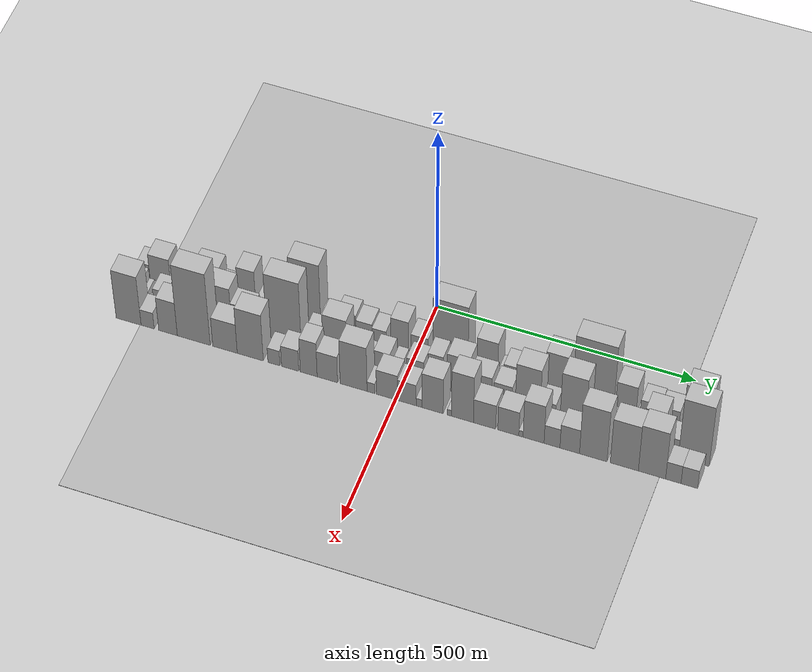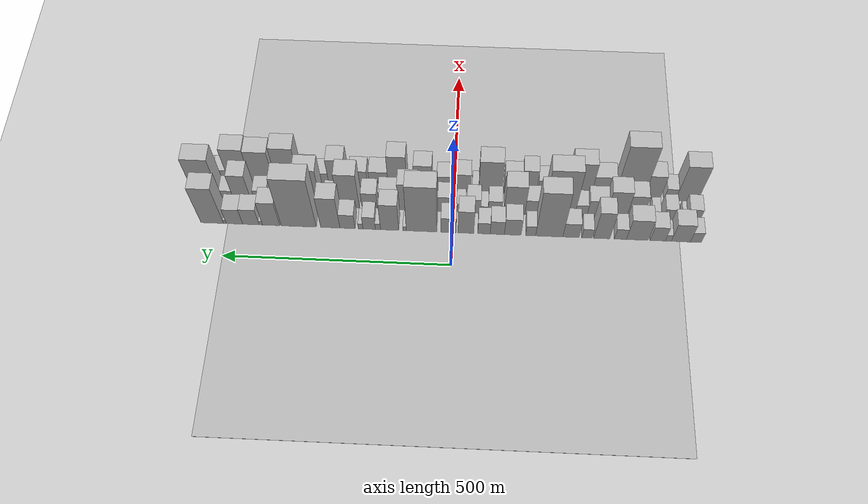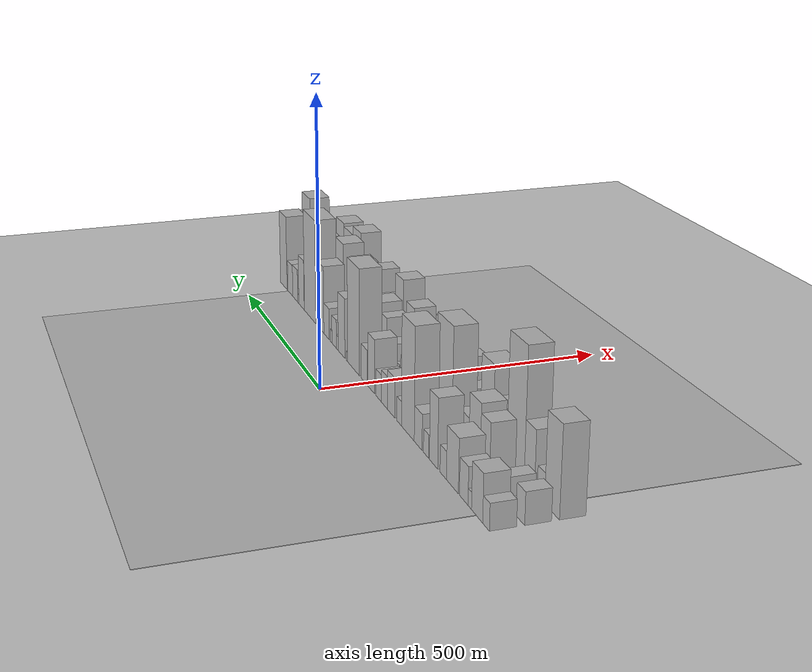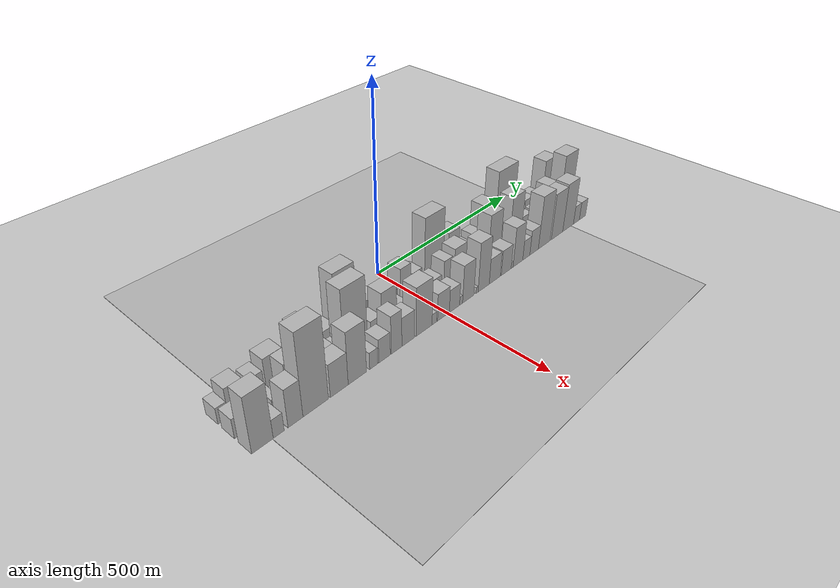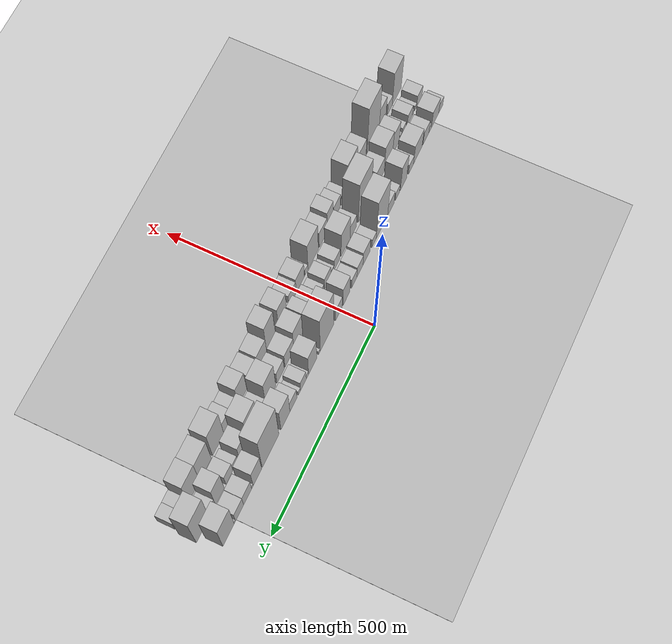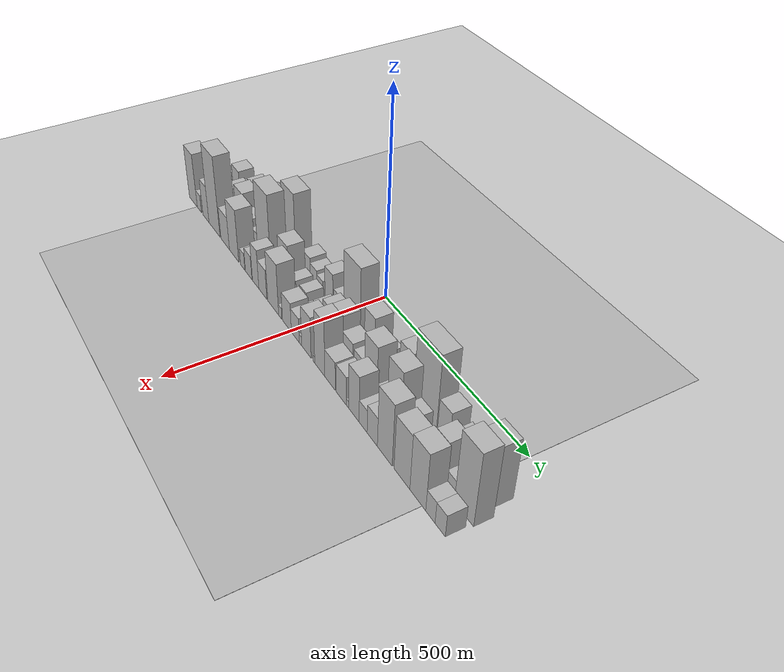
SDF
<?xml version="1.0" encoding="utf-8"?>

<sdf version="1.6">

   <world name="default">

      <gui fullscreen="0">

         <camera name="user_camera">

            <pose>-15 0 4.57585 0 0 0</pose>

            <view_controller>orbit</view_controller>

         </camera>

      </gui>

      <scene>

         <sky>

           <clouds>

             <speed>12</speed>

           </clouds>

         </sky>

         <ambient>0.4 0.4 0.4 1</ambient>

         <background>0.7 0.7 0.7 1</background>

         <shadows>1</shadows>

      </scene>

      <gravity>0 0 -9.8066</gravity>

      <magnetic_field>6e-06 2.3e-05 -4.2e-05</magnetic_field>

      <physics default="0" name="default_physics" type="ode">

         <ode>

            <solver>

               <type>quick</type>

               <iters>10</iters>

               <sor>1.0</sor>

               <use_dynamic_moi_rescaling>0</use_dynamic_moi_rescaling>

            </solver>

            <constraints>

               <cfm>0</cfm>

               <erp>0.2</erp>

               <contact_max_correcting_vel>100</contact_max_correcting_vel>

               <contact_surface_layer>0.001</contact_surface_layer>

            </constraints>

         </ode>

         <max_step_size>0.004</max_step_size>

         <real_time_factor>1</real_time_factor>

         <real_time_update_rate>250</real_time_update_rate>

      </physics>

      <light name="sun" type="directional">

         <cast_shadows>1</cast_shadows>

         <pose>0 0 10 0 0 0</pose>

         <diffuse>0.8 0.8 0.8 1</diffuse>

         <specular>0.2 0.2 0.2 1</specular>

         <attenuation>

            <range>1000</range>

            <constant>0.9</constant>

            <linear>0.01</linear>

            <quadratic>0.001</quadratic>

         </attenuation>

         <direction>-0.5 0.1 -0.9</direction>

      </light>

      <include>

         <name>ground_plane_1</name>

         <uri>model://HANNAS_ground_plane</uri>

         <pose>0 0 0  0 0 0</pose>

      </include>

      <include>

         <name>ground_plane_2</name>

         <uri>model://HANNAS_ground_plane</uri>

         <pose>100 0 0  0 0 0</pose>

      </include>

      <model name="building_1">

         <static>1</static>

         <pose frame="">100.0000 -535.8190 0 0.000000 0.000000 0.000000</pose>

         <link name="link">

            <pose frame="">0 0 21.00 0 0 0</pose>

            <collision name="collision">

               <geometry>

                  <box>

                     <size>40.0000 24.3621 42.0000</size>

                  </box>

               </geometry>

               <max_contacts>10</max_contacts>

               <surface>

                  <contact>

                     <ode/>

                  </contact>

                  <bounce/>

                  <friction>

                     <torsional>

                        <ode/>

                     </torsional>

                     <ode/>

                  </friction>

               </surface>

            </collision>

            <visual name="visual">

               <cast_shadows>0</cast_shadows>

               <geometry>

                  <box>

                     <size>40.0000 24.3621 42.0000</size>

                  </box>

               </geometry>

               <material>

                  <script>

                     <uri>model://HANNAS_wall/materials/scripts</uri>

                     <uri>model://HANNAS_wall/materials/textures</uri>

                     <name>vrc/HANNAS_wall</name>

                  </script>

               </material>

            </visual>

            <self_collide>0</self_collide>

            <enable_wind>0</enable_wind>

            <kinematic>0</kinematic>

         </link>

      </model>

      <model name="building_2">

         <static>1</static>

         <pose frame="">100.0000 -502.9617 0 0.000000 0.000000 0.000000</pose>

         <link name="link">

            <pose frame="">0 0 37.50 0 0 0</pose>

            <collision name="collision">

               <geometry>

                  <box>

                     <size>40.0000 41.3526 75.0000</size>

                  </box>

               </geometry>

               <max_contacts>10</max_contacts>

               <surface>

                  <contact>

                     <ode/>

                  </contact>

                  <bounce/>

                  <friction>

                     <torsional>

                        <ode/>

                     </torsional>

                     <ode/>

                  </friction>

               </surface>

            </collision>

            <visual name="visual">

               <cast_shadows>0</cast_shadows>

               <geometry>

                  <box>

                     <size>40.0000 41.3526 75.0000</size>

                  </box>

               </geometry>

               <material>

                  <script>

                     <uri>model://HANNAS_wall/materials/scripts</uri>

                     <uri>model://HANNAS_wall/materials/textures</uri>

                     <name>vrc/HANNAS_wall</name>

                  </script>

               </material>

            </visual>

            <self_collide>0</self_collide>

            <enable_wind>0</enable_wind>

            <kinematic>0</kinematic>

         </link>

      </model>

      <model name="building_3">

         <static>1</static>

         <pose frame="">100.0000 -475.5732 0 0.000000 0.000000 0.000000</pose>

         <link name="link">

            <pose frame="">0 0 13.50 0 0 0</pose>

            <collision name="collision">

               <geometry>

                  <box>

                     <size>40.0000 13.4244 27.0000</size>

                  </box>

               </geometry>

               <max_contacts>10</max_contacts>

               <surface>

                  <contact>

                     <ode/>

                  </contact>

                  <bounce/>

                  <friction>

                     <torsional>

                        <ode/>

                     </torsional>

                     <ode/>

                  </friction>

               </surface>

            </collision>

            <visual name="visual">

               <cast_shadows>0</cast_shadows>

               <geometry>

                  <box>

                     <size>40.0000 13.4244 27.0000</size>

                  </box>

               </geometry>

               <material>

                  <script>

                     <uri>model://HANNAS_wall/materials/scripts</uri>

                     <uri>model://HANNAS_wall/materials/textures</uri>

                     <name>vrc/HANNAS_wall</name>

                  </script>

               </material>

            </visual>

            <self_collide>0</self_collide>

            <enable_wind>0</enable_wind>

            <kinematic>0</kinematic>

         </link>

      </model>

      <model name="building_4">

         <static>1</static>

         <pose frame="">100.0000 -452.2671 0 0.000000 0.000000 0.000000</pose>

         <link name="link">

            <pose frame="">0 0 30.00 0 0 0</pose>

            <collision name="collision">

               <geometry>

                  <box>

                     <size>40.0000 33.1878 60.0000</size>

                  </box>

               </geometry>

               <max_contacts>10</max_contacts>

               <surface>

                  <contact>

                     <ode/>

                  </contact>

                  <bounce/>

                  <friction>

                     <torsional>

                        <ode/>

                     </torsional>

                     <ode/>

                  </friction>

               </surface>

            </collision>

            <visual name="visual">

               <cast_shadows>0</cast_shadows>

               <geometry>

                  <box>

                     <size>40.0000 33.1878 60.0000</size>

                  </box>

               </geometry>

               <material>

                  <script>

                     <uri>model://HANNAS_wall/materials/scripts</uri>

                     <uri>model://HANNAS_wall/materials/textures</uri>

                     <name>vrc/HANNAS_wall</name>

                  </script>

               </material>

            </visual>

            <self_collide>0</self_collide>

            <enable_wind>0</enable_wind>

            <kinematic>0</kinematic>

         </link>

      </model>

      <model name="building_5">

         <static>1</static>

         <pose frame="">100.0000 -407.6439 0 0.000000 0.000000 0.000000</pose>

         <link name="link">

            <pose frame="">0 0 43.50 0 0 0</pose>

            <collision name="collision">

               <geometry>

                  <box>

                     <size>40.0000 48.0586 87.0000</size>

                  </box>

               </geometry>

               <max_contacts>10</max_contacts>

               <surface>

                  <contact>

                     <ode/>

                  </contact>

                  <bounce/>

                  <friction>

                     <torsional>

                        <ode/>

                     </torsional>

                     <ode/>

                  </friction>

               </surface>

            </collision>

            <visual name="visual">

               <cast_shadows>0</cast_shadows>

               <geometry>

                  <box>

                     <size>40.0000 48.0586 87.0000</size>

                  </box>

               </geometry>

               <material>

                  <script>

                     <uri>model://HANNAS_wall/materials/scripts</uri>

                     <uri>model://HANNAS_wall/materials/textures</uri>

                     <name>vrc/HANNAS_wall</name>

                  </script>

               </material>

            </visual>

            <self_collide>0</self_collide>

            <enable_wind>0</enable_wind>

            <kinematic>0</kinematic>

         </link>

      </model>

      <model name="building_6">

         <static>1</static>

         <pose frame="">100.0000 -370.3365 0 0.000000 0.000000 0.000000</pose>

         <link name="link">

            <pose frame="">0 0 22.50 0 0 0</pose>

            <collision name="collision">

               <geometry>

                  <box>

                     <size>40.0000 26.5561 45.0000</size>

                  </box>

               </geometry>

               <max_contacts>10</max_contacts>

               <surface>

                  <contact>

                     <ode/>

                  </contact>

                  <bounce/>

                  <friction>

                     <torsional>

                        <ode/>

                     </torsional>

                     <ode/>

                  </friction>

               </surface>

            </collision>

            <visual name="visual">

               <cast_shadows>0</cast_shadows>

               <geometry>

                  <box>

                     <size>40.0000 26.5561 45.0000</size>

                  </box>

               </geometry>

               <material>

                  <script>

                     <uri>model://HANNAS_wall/materials/scripts</uri>

                     <uri>model://HANNAS_wall/materials/textures</uri>

                     <name>vrc/HANNAS_wall</name>

                  </script>

               </material>

            </visual>

            <self_collide>0</self_collide>

            <enable_wind>0</enable_wind>

            <kinematic>0</kinematic>

         </link>

      </model>

      <model name="building_7">

         <static>1</static>

         <pose frame="">100.0000 -329.3796 0 0.000000 0.000000 0.000000</pose>

         <link name="link">

            <pose frame="">0 0 57.00 0 0 0</pose>

            <collision name="collision">

               <geometry>

                  <box>

                     <size>40.0000 35.3578 114.0000</size>

                  </box>

               </geometry>

               <max_contacts>10</max_contacts>

               <surface>

                  <contact>

                     <ode/>

                  </contact>

                  <bounce/>

                  <friction>

                     <torsional>

                        <ode/>

                     </torsional>

                     <ode/>

                  </friction>

               </surface>

            </collision>

            <visual name="visual">

               <cast_shadows>0</cast_shadows>

               <geometry>

                  <box>

                     <size>40.0000 35.3578 114.0000</size>

                  </box>

               </geometry>

               <material>

                  <script>

                     <uri>model://HANNAS_wall/materials/scripts</uri>

                     <uri>model://HANNAS_wall/materials/textures</uri>

                     <name>vrc/HANNAS_wall</name>

                  </script>

               </material>

            </visual>

            <self_collide>0</self_collide>

            <enable_wind>0</enable_wind>

            <kinematic>0</kinematic>

         </link>

      </model>

      <model name="building_8">

         <static>1</static>

         <pose frame="">100.0000 -297.0140 0 0.000000 0.000000 0.000000</pose>

         <link name="link">

            <pose frame="">0 0 19.50 0 0 0</pose>

            <collision name="collision">

               <geometry>

                  <box>

                     <size>40.0000 23.3734 39.0000</size>

                  </box>

               </geometry>

               <max_contacts>10</max_contacts>

               <surface>

                  <contact>

                     <ode/>

                  </contact>

                  <bounce/>

                  <friction>

                     <torsional>

                        <ode/>

                     </torsional>

                     <ode/>

                  </friction>

               </surface>

            </collision>

            <visual name="visual">

               <cast_shadows>0</cast_shadows>

               <geometry>

                  <box>

                     <size>40.0000 23.3734 39.0000</size>

                  </box>

               </geometry>

               <material>

                  <script>

                     <uri>model://HANNAS_wall/materials/scripts</uri>

                     <uri>model://HANNAS_wall/materials/textures</uri>

                     <name>vrc/HANNAS_wall</name>

                  </script>

               </material>

            </visual>

            <self_collide>0</self_collide>

            <enable_wind>0</enable_wind>

            <kinematic>0</kinematic>

         </link>

      </model>

      <model name="building_9">

         <static>1</static>

         <pose frame="">100.0000 -261.6188 0 0.000000 0.000000 0.000000</pose>

         <link name="link">

            <pose frame="">0 0 30.00 0 0 0</pose>

            <collision name="collision">

               <geometry>

                  <box>

                     <size>40.0000 35.4170 60.0000</size>

                  </box>

               </geometry>

               <max_contacts>10</max_contacts>

               <surface>

                  <contact>

                     <ode/>

                  </contact>

                  <bounce/>

                  <friction>

                     <torsional>

                        <ode/>

                     </torsional>

                     <ode/>

                  </friction>

               </surface>

            </collision>

            <visual name="visual">

               <cast_shadows>0</cast_shadows>

               <geometry>

                  <box>

                     <size>40.0000 35.4170 60.0000</size>

                  </box>

               </geometry>

               <material>

                  <script>

                     <uri>model://HANNAS_wall/materials/scripts</uri>

                     <uri>model://HANNAS_wall/materials/textures</uri>

                     <name>vrc/HANNAS_wall</name>

                  </script>

               </material>

            </visual>

            <self_collide>0</self_collide>

            <enable_wind>0</enable_wind>

            <kinematic>0</kinematic>

         </link>

      </model>

      <model name="building_10">

         <static>1</static>

         <pose frame="">100.0000 -213.8391 0 0.000000 0.000000 0.000000</pose>

         <link name="link">

            <pose frame="">0 0 94.50 0 0 0</pose>

            <collision name="collision">

               <geometry>

                  <box>

                     <size>40.0000 60.1424 189.0000</size>

                  </box>

               </geometry>

               <max_contacts>10</max_contacts>

               <surface>

                  <contact>

                     <ode/>

                  </contact>

                  <bounce/>

                  <friction>

                     <torsional>

                        <ode/>

                     </torsional>

                     <ode/>

                  </friction>

               </surface>

            </collision>

            <visual name="visual">

               <cast_shadows>0</cast_shadows>

               <geometry>

                  <box>

                     <size>40.0000 60.1424 189.0000</size>

                  </box>

               </geometry>

               <material>

                  <script>

                     <uri>model://HANNAS_wall/materials/scripts</uri>

                     <uri>model://HANNAS_wall/materials/textures</uri>

                     <name>vrc/HANNAS_wall</name>

                  </script>

               </material>

            </visual>

            <self_collide>0</self_collide>

            <enable_wind>0</enable_wind>

            <kinematic>0</kinematic>

         </link>

      </model>

      <model name="building_11">

         <static>1</static>

         <pose frame="">100.0000 -172.6313 0 0.000000 0.000000 0.000000</pose>

         <link name="link">

            <pose frame="">0 0 21.00 0 0 0</pose>

            <collision name="collision">

               <geometry>

                  <box>

                     <size>40.0000 22.2732 42.0000</size>

                  </box>

               </geometry>

               <max_contacts>10</max_contacts>

               <surface>

                  <contact>

                     <ode/>

                  </contact>

                  <bounce/>

                  <friction>

                     <torsional>

                        <ode/>

                     </torsional>

                     <ode/>

                  </friction>

               </surface>

            </collision>

            <visual name="visual">

               <cast_shadows>0</cast_shadows>

               <geometry>

                  <box>

                     <size>40.0000 22.2732 42.0000</size>

                  </box>

               </geometry>

               <material>

                  <script>

                     <uri>model://HANNAS_wall/materials/scripts</uri>

                     <uri>model://HANNAS_wall/materials/textures</uri>

                     <name>vrc/HANNAS_wall</name>

                  </script>

               </material>

            </visual>

            <self_collide>0</self_collide>

            <enable_wind>0</enable_wind>

            <kinematic>0</kinematic>

         </link>

      </model>

      <model name="building_12">

         <static>1</static>

         <pose frame="">100.0000 -133.0729 0 0.000000 0.000000 0.000000</pose>

         <link name="link">

            <pose frame="">0 0 34.50 0 0 0</pose>

            <collision name="collision">

               <geometry>

                  <box>

                     <size>40.0000 36.8435 69.0000</size>

                  </box>

               </geometry>

               <max_contacts>10</max_contacts>

               <surface>

                  <contact>

                     <ode/>

                  </contact>

                  <bounce/>

                  <friction>

                     <torsional>

                        <ode/>

                     </torsional>

                     <ode/>

                  </friction>

               </surface>

            </collision>

            <visual name="visual">

               <cast_shadows>0</cast_shadows>

               <geometry>

                  <box>

                     <size>40.0000 36.8435 69.0000</size>

                  </box>

               </geometry>

               <material>

                  <script>

                     <uri>model://HANNAS_wall/materials/scripts</uri>

                     <uri>model://HANNAS_wall/materials/textures</uri>

                     <name>vrc/HANNAS_wall</name>

                  </script>

               </material>

            </visual>

            <self_collide>0</self_collide>

            <enable_wind>0</enable_wind>

            <kinematic>0</kinematic>

         </link>

      </model>

      <model name="building_13">

         <static>1</static>

         <pose frame="">100.0000 -98.9799 0 0.000000 0.000000 0.000000</pose>

         <link name="link">

            <pose frame="">0 0 28.50 0 0 0</pose>

            <collision name="collision">

               <geometry>

                  <box>

                     <size>40.0000 31.3427 57.0000</size>

                  </box>

               </geometry>

               <max_contacts>10</max_contacts>

               <surface>

                  <contact>

                     <ode/>

                  </contact>

                  <bounce/>

                  <friction>

                     <torsional>

                        <ode/>

                     </torsional>

                     <ode/>

                  </friction>

               </surface>

            </collision>

            <visual name="visual">

               <cast_shadows>0</cast_shadows>

               <geometry>

                  <box>

                     <size>40.0000 31.3427 57.0000</size>

                  </box>

               </geometry>

               <material>

                  <script>

                     <uri>model://HANNAS_wall/materials/scripts</uri>

                     <uri>model://HANNAS_wall/materials/textures</uri>

                     <name>vrc/HANNAS_wall</name>

                  </script>

               </material>

            </visual>

            <self_collide>0</self_collide>

            <enable_wind>0</enable_wind>

            <kinematic>0</kinematic>

         </link>

      </model>

      <model name="building_14">

         <static>1</static>

         <pose frame="">100.0000 -69.6493 0 0.000000 0.000000 0.000000</pose>

         <link name="link">

            <pose frame="">0 0 24.00 0 0 0</pose>

            <collision name="collision">

               <geometry>

                  <box>

                     <size>40.0000 27.3186 48.0000</size>

                  </box>

               </geometry>

               <max_contacts>10</max_contacts>

               <surface>

                  <contact>

                     <ode/>

                  </contact>

                  <bounce/>

                  <friction>

                     <torsional>

                        <ode/>

                     </torsional>

                     <ode/>

                  </friction>

               </surface>

            </collision>

            <visual name="visual">

               <cast_shadows>0</cast_shadows>

               <geometry>

                  <box>

                     <size>40.0000 27.3186 48.0000</size>

                  </box>

               </geometry>

               <material>

                  <script>

                     <uri>model://HANNAS_wall/materials/scripts</uri>

                     <uri>model://HANNAS_wall/materials/textures</uri>

                     <name>vrc/HANNAS_wall</name>

                  </script>

               </material>

            </visual>

            <self_collide>0</self_collide>

            <enable_wind>0</enable_wind>

            <kinematic>0</kinematic>

         </link>

      </model>

      <model name="building_15">

         <static>1</static>

         <pose frame="">100.0000 -29.5580 0 0.000000 0.000000 0.000000</pose>

         <link name="link">

            <pose frame="">0 0 48.00 0 0 0</pose>

            <collision name="collision">

               <geometry>

                  <box>

                     <size>40.0000 34.8640 96.0000</size>

                  </box>

               </geometry>

               <max_contacts>10</max_contacts>

               <surface>

                  <contact>

                     <ode/>

                  </contact>

                  <bounce/>

                  <friction>

                     <torsional>

                        <ode/>

                     </torsional>

                     <ode/>

                  </friction>

               </surface>

            </collision>

            <visual name="visual">

               <cast_shadows>0</cast_shadows>

               <geometry>

                  <box>

                     <size>40.0000 34.8640 96.0000</size>

                  </box>

               </geometry>

               <material>

                  <script>

                     <uri>model://HANNAS_wall/materials/scripts</uri>

                     <uri>model://HANNAS_wall/materials/textures</uri>

                     <name>vrc/HANNAS_wall</name>

                  </script>

               </material>

            </visual>

            <self_collide>0</self_collide>

            <enable_wind>0</enable_wind>

            <kinematic>0</kinematic>

         </link>

      </model>

      <model name="building_16">

         <static>1</static>

         <pose frame="">100.0000 8.8448 0 0.000000 0.000000 0.000000</pose>

         <link name="link">

            <pose frame="">0 0 31.50 0 0 0</pose>

            <collision name="collision">

               <geometry>

                  <box>

                     <size>40.0000 33.9415 63.0000</size>

                  </box>

               </geometry>

               <max_contacts>10</max_contacts>

               <surface>

                  <contact>

                     <ode/>

                  </contact>

                  <bounce/>

                  <friction>

                     <torsional>

                        <ode/>

                     </torsional>

                     <ode/>

                  </friction>

               </surface>

            </collision>

            <visual name="visual">

               <cast_shadows>0</cast_shadows>

               <geometry>

                  <box>

                     <size>40.0000 33.9415 63.0000</size>

                  </box>

               </geometry>

               <material>

                  <script>

                     <uri>model://HANNAS_wall/materials/scripts</uri>

                     <uri>model://HANNAS_wall/materials/textures</uri>

                     <name>vrc/HANNAS_wall</name>

                  </script>

               </material>

            </visual>

            <self_collide>0</self_collide>

            <enable_wind>0</enable_wind>

            <kinematic>0</kinematic>

         </link>

      </model>

      <model name="building_17">

         <static>1</static>

         <pose frame="">100.0000 68.5710 0 0.000000 0.000000 0.000000</pose>

         <link name="link">

            <pose frame="">0 0 96.00 0 0 0</pose>

            <collision name="collision">

               <geometry>

                  <box>

                     <size>40.0000 67.5108 192.0000</size>

                  </box>

               </geometry>

               <max_contacts>10</max_contacts>

               <surface>

                  <contact>

                     <ode/>

                  </contact>

                  <bounce/>

                  <friction>

                     <torsional>

                        <ode/>

                     </torsional>

                     <ode/>

                  </friction>

               </surface>

            </collision>

            <visual name="visual">

               <cast_shadows>0</cast_shadows>

               <geometry>

                  <box>

                     <size>40.0000 67.5108 192.0000</size>

                  </box>

               </geometry>

               <material>

                  <script>

                     <uri>model://HANNAS_wall/materials/scripts</uri>

                     <uri>model://HANNAS_wall/materials/textures</uri>

                     <name>vrc/HANNAS_wall</name>

                  </script>

               </material>

            </visual>

            <self_collide>0</self_collide>

            <enable_wind>0</enable_wind>

            <kinematic>0</kinematic>

         </link>

      </model>

      <model name="building_18">

         <static>1</static>

         <pose frame="">100.0000 106.2454 0 0.000000 0.000000 0.000000</pose>

         <link name="link">

            <pose frame="">0 0 9.00 0 0 0</pose>

            <collision name="collision">

               <geometry>

                  <box>

                     <size>40.0000 7.8379 18.0000</size>

                  </box>

               </geometry>

               <max_contacts>10</max_contacts>

               <surface>

                  <contact>

                     <ode/>

                  </contact>

                  <bounce/>

                  <friction>

                     <torsional>

                        <ode/>

                     </torsional>

                     <ode/>

                  </friction>

               </surface>

            </collision>

            <visual name="visual">

               <cast_shadows>0</cast_shadows>

               <geometry>

                  <box>

                     <size>40.0000 7.8379 18.0000</size>

                  </box>

               </geometry>

               <material>

                  <script>

                     <uri>model://HANNAS_wall/materials/scripts</uri>

                     <uri>model://HANNAS_wall/materials/textures</uri>

                     <name>vrc/HANNAS_wall</name>

                  </script>

               </material>

            </visual>

            <self_collide>0</self_collide>

            <enable_wind>0</enable_wind>

            <kinematic>0</kinematic>

         </link>

      </model>

      <model name="building_19">

         <static>1</static>

         <pose frame="">100.0000 139.3335 0 0.000000 0.000000 0.000000</pose>

         <link name="link">

            <pose frame="">0 0 55.50 0 0 0</pose>

            <collision name="collision">

               <geometry>

                  <box>

                     <size>40.0000 40.3383 111.0000</size>

                  </box>

               </geometry>

               <max_contacts>10</max_contacts>

               <surface>

                  <contact>

                     <ode/>

                  </contact>

                  <bounce/>

                  <friction>

                     <torsional>

                        <ode/>

                     </torsional>

                     <ode/>

                  </friction>

               </surface>

            </collision>

            <visual name="visual">

               <cast_shadows>0</cast_shadows>

               <geometry>

                  <box>

                     <size>40.0000 40.3383 111.0000</size>

                  </box>

               </geometry>

               <material>

                  <script>

                     <uri>model://HANNAS_wall/materials/scripts</uri>

                     <uri>model://HANNAS_wall/materials/textures</uri>

                     <name>vrc/HANNAS_wall</name>

                  </script>

               </material>

            </visual>

            <self_collide>0</self_collide>

            <enable_wind>0</enable_wind>

            <kinematic>0</kinematic>

         </link>

      </model>

      <model name="building_20">

         <static>1</static>

         <pose frame="">100.0000 165.2207 0 0.000000 0.000000 0.000000</pose>

         <link name="link">

            <pose frame="">0 0 13.50 0 0 0</pose>

            <collision name="collision">

               <geometry>

                  <box>

                     <size>40.0000 11.4361 27.0000</size>

                  </box>

               </geometry>

               <max_contacts>10</max_contacts>

               <surface>

                  <contact>

                     <ode/>

                  </contact>

                  <bounce/>

                  <friction>

                     <torsional>

                        <ode/>

                     </torsional>

                     <ode/>

                  </friction>

               </surface>

            </collision>

            <visual name="visual">

               <cast_shadows>0</cast_shadows>

               <geometry>

                  <box>

                     <size>40.0000 11.4361 27.0000</size>

                  </box>

               </geometry>

               <material>

                  <script>

                     <uri>model://HANNAS_wall/materials/scripts</uri>

                     <uri>model://HANNAS_wall/materials/textures</uri>

                     <name>vrc/HANNAS_wall</name>

                  </script>

               </material>

            </visual>

            <self_collide>0</self_collide>

            <enable_wind>0</enable_wind>

            <kinematic>0</kinematic>

         </link>

      </model>

      <model name="building_21">

         <static>1</static>

         <pose frame="">100.0000 184.7017 0 0.000000 0.000000 0.000000</pose>

         <link name="link">

            <pose frame="">0 0 27.00 0 0 0</pose>

            <collision name="collision">

               <geometry>

                  <box>

                     <size>40.0000 27.5259 54.0000</size>

                  </box>

               </geometry>

               <max_contacts>10</max_contacts>

               <surface>

                  <contact>

                     <ode/>

                  </contact>

                  <bounce/>

                  <friction>

                     <torsional>

                        <ode/>

                     </torsional>

                     <ode/>

                  </friction>

               </surface>

            </collision>

            <visual name="visual">

               <cast_shadows>0</cast_shadows>

               <geometry>

                  <box>

                     <size>40.0000 27.5259 54.0000</size>

                  </box>

               </geometry>

               <material>

                  <script>

                     <uri>model://HANNAS_wall/materials/scripts</uri>

                     <uri>model://HANNAS_wall/materials/textures</uri>

                     <name>vrc/HANNAS_wall</name>

                  </script>

               </material>

            </visual>

            <self_collide>0</self_collide>

            <enable_wind>0</enable_wind>

            <kinematic>0</kinematic>

         </link>

      </model>

      <model name="building_22">

         <static>1</static>

         <pose frame="">100.0000 203.6912 0 0.000000 0.000000 0.000000</pose>

         <link name="link">

            <pose frame="">0 0 12.00 0 0 0</pose>

            <collision name="collision">

               <geometry>

                  <box>

                     <size>40.0000 10.4531 24.0000</size>

                  </box>

               </geometry>

               <max_contacts>10</max_contacts>

               <surface>

                  <contact>

                     <ode/>

                  </contact>

                  <bounce/>

                  <friction>

                     <torsional>

                        <ode/>

                     </torsional>

                     <ode/>

                  </friction>

               </surface>

            </collision>

            <visual name="visual">

               <cast_shadows>0</cast_shadows>

               <geometry>

                  <box>

                     <size>40.0000 10.4531 24.0000</size>

                  </box>

               </geometry>

               <material>

                  <script>

                     <uri>model://HANNAS_wall/materials/scripts</uri>

                     <uri>model://HANNAS_wall/materials/textures</uri>

                     <name>vrc/HANNAS_wall</name>

                  </script>

               </material>

            </visual>

            <self_collide>0</self_collide>

            <enable_wind>0</enable_wind>

            <kinematic>0</kinematic>

         </link>

      </model>

      <model name="building_23">

         <static>1</static>

         <pose frame="">100.0000 232.8153 0 0.000000 0.000000 0.000000</pose>

         <link name="link">

            <pose frame="">0 0 30.00 0 0 0</pose>

            <collision name="collision">

               <geometry>

                  <box>

                     <size>40.0000 33.7951 60.0000</size>

                  </box>

               </geometry>

               <max_contacts>10</max_contacts>

               <surface>

                  <contact>

                     <ode/>

                  </contact>

                  <bounce/>

                  <friction>

                     <torsional>

                        <ode/>

                     </torsional>

                     <ode/>

                  </friction>

               </surface>

            </collision>

            <visual name="visual">

               <cast_shadows>0</cast_shadows>

               <geometry>

                  <box>

                     <size>40.0000 33.7951 60.0000</size>

                  </box>

               </geometry>

               <material>

                  <script>

                     <uri>model://HANNAS_wall/materials/scripts</uri>

                     <uri>model://HANNAS_wall/materials/textures</uri>

                     <name>vrc/HANNAS_wall</name>

                  </script>

               </material>

            </visual>

            <self_collide>0</self_collide>

            <enable_wind>0</enable_wind>

            <kinematic>0</kinematic>

         </link>

      </model>

      <model name="building_24">

         <static>1</static>

         <pose frame="">100.0000 271.0639 0 0.000000 0.000000 0.000000</pose>

         <link name="link">

            <pose frame="">0 0 64.50 0 0 0</pose>

            <collision name="collision">

               <geometry>

                  <box>

                     <size>40.0000 42.7021 129.0000</size>

                  </box>

               </geometry>

               <max_contacts>10</max_contacts>

               <surface>

                  <contact>

                     <ode/>

                  </contact>

                  <bounce/>

                  <friction>

                     <torsional>

                        <ode/>

                     </torsional>

                     <ode/>

                  </friction>

               </surface>

            </collision>

            <visual name="visual">

               <cast_shadows>0</cast_shadows>

               <geometry>

                  <box>

                     <size>40.0000 42.7021 129.0000</size>

                  </box>

               </geometry>

               <material>

                  <script>

                     <uri>model://HANNAS_wall/materials/scripts</uri>

                     <uri>model://HANNAS_wall/materials/textures</uri>

                     <name>vrc/HANNAS_wall</name>

                  </script>

               </material>

            </visual>

            <self_collide>0</self_collide>

            <enable_wind>0</enable_wind>

            <kinematic>0</kinematic>

         </link>

      </model>

      <model name="building_25">

         <static>1</static>

         <pose frame="">100.0000 341.4721 0 0.000000 0.000000 0.000000</pose>

         <link name="link">

            <pose frame="">0 0 100.50 0 0 0</pose>

            <collision name="collision">

               <geometry>

                  <box>

                     <size>40.0000 78.1143 201.0000</size>

                  </box>

               </geometry>

               <max_contacts>10</max_contacts>

               <surface>

                  <contact>

                     <ode/>

                  </contact>

                  <bounce/>

                  <friction>

                     <torsional>

                        <ode/>

                     </torsional>

                     <ode/>

                  </friction>

               </surface>

            </collision>

            <visual name="visual">

               <cast_shadows>0</cast_shadows>

               <geometry>

                  <box>

                     <size>40.0000 78.1143 201.0000</size>

                  </box>

               </geometry>

               <material>

                  <script>

                     <uri>model://HANNAS_wall/materials/scripts</uri>

                     <uri>model://HANNAS_wall/materials/textures</uri>

                     <name>vrc/HANNAS_wall</name>

                  </script>

               </material>

            </visual>

            <self_collide>0</self_collide>

            <enable_wind>0</enable_wind>

            <kinematic>0</kinematic>

         </link>

      </model>

      <model name="building_26">

         <static>1</static>

         <pose frame="">100.0000 403.0197 0 0.000000 0.000000 0.000000</pose>

         <link name="link">

            <pose frame="">0 0 49.50 0 0 0</pose>

            <collision name="collision">

               <geometry>

                  <box>

                     <size>40.0000 38.9808 99.0000</size>

                  </box>

               </geometry>

               <max_contacts>10</max_contacts>

               <surface>

                  <contact>

                     <ode/>

                  </contact>

                  <bounce/>

                  <friction>

                     <torsional>

                        <ode/>

                     </torsional>

                     <ode/>

                  </friction>

               </surface>

            </collision>

            <visual name="visual">

               <cast_shadows>0</cast_shadows>

               <geometry>

                  <box>

                     <size>40.0000 38.9808 99.0000</size>

                  </box>

               </geometry>

               <material>

                  <script>

                     <uri>model://HANNAS_wall/materials/scripts</uri>

                     <uri>model://HANNAS_wall/materials/textures</uri>

                     <name>vrc/HANNAS_wall</name>

                  </script>

               </material>

            </visual>

            <self_collide>0</self_collide>

            <enable_wind>0</enable_wind>

            <kinematic>0</kinematic>

         </link>

      </model>

      <model name="building_27">

         <static>1</static>

         <pose frame="">100.0000 426.1616 0 0.000000 0.000000 0.000000</pose>

         <link name="link">

            <pose frame="">0 0 9.00 0 0 0</pose>

            <collision name="collision">

               <geometry>

                  <box>

                     <size>40.0000 7.3030 18.0000</size>

                  </box>

               </geometry>

               <max_contacts>10</max_contacts>

               <surface>

                  <contact>

                     <ode/>

                  </contact>

                  <bounce/>

                  <friction>

                     <torsional>

                        <ode/>

                     </torsional>

                     <ode/>

                  </friction>

               </surface>

            </collision>

            <visual name="visual">

               <cast_shadows>0</cast_shadows>

               <geometry>

                  <box>

                     <size>40.0000 7.3030 18.0000</size>

                  </box>

               </geometry>

               <material>

                  <script>

                     <uri>model://HANNAS_wall/materials/scripts</uri>

                     <uri>model://HANNAS_wall/materials/textures</uri>

                     <name>vrc/HANNAS_wall</name>

                  </script>

               </material>

            </visual>

            <self_collide>0</self_collide>

            <enable_wind>0</enable_wind>

            <kinematic>0</kinematic>

         </link>

      </model>

      <model name="building_28">

         <static>1</static>

         <pose frame="">100.0000 448.1309 0 0.000000 0.000000 0.000000</pose>

         <link name="link">

            <pose frame="">0 0 33.00 0 0 0</pose>

            <collision name="collision">

               <geometry>

                  <box>

                     <size>40.0000 36.6356 66.0000</size>

                  </box>

               </geometry>

               <max_contacts>10</max_contacts>

               <surface>

                  <contact>

                     <ode/>

                  </contact>

                  <bounce/>

                  <friction>

                     <torsional>

                        <ode/>

                     </torsional>

                     <ode/>

                  </friction>

               </surface>

            </collision>

            <visual name="visual">

               <cast_shadows>0</cast_shadows>

               <geometry>

                  <box>

                     <size>40.0000 36.6356 66.0000</size>

                  </box>

               </geometry>

               <material>

                  <script>

                     <uri>model://HANNAS_wall/materials/scripts</uri>

                     <uri>model://HANNAS_wall/materials/textures</uri>

                     <name>vrc/HANNAS_wall</name>

                  </script>

               </material>

            </visual>

            <self_collide>0</self_collide>

            <enable_wind>0</enable_wind>

            <kinematic>0</kinematic>

         </link>

      </model>

      <model name="building_29">

         <static>1</static>

         <pose frame="">100.0000 484.8360 0 0.000000 0.000000 0.000000</pose>

         <link name="link">

            <pose frame="">0 0 31.50 0 0 0</pose>

            <collision name="collision">

               <geometry>

                  <box>

                     <size>40.0000 36.7747 63.0000</size>

                  </box>

               </geometry>

               <max_contacts>10</max_contacts>

               <surface>

                  <contact>

                     <ode/>

                  </contact>

                  <bounce/>

                  <friction>

                     <torsional>

                        <ode/>

                     </torsional>

                     <ode/>

                  </friction>

               </surface>

            </collision>

            <visual name="visual">

               <cast_shadows>0</cast_shadows>

               <geometry>

                  <box>

                     <size>40.0000 36.7747 63.0000</size>

                  </box>

               </geometry>

               <material>

                  <script>

                     <uri>model://HANNAS_wall/materials/scripts</uri>

                     <uri>model://HANNAS_wall/materials/textures</uri>

                     <name>vrc/HANNAS_wall</name>

                  </script>

               </material>

            </visual>

            <self_collide>0</self_collide>

            <enable_wind>0</enable_wind>

            <kinematic>0</kinematic>

         </link>

      </model>

      <model name="building_30">

         <static>1</static>

         <pose frame="">100.0000 506.3536 0 0.000000 0.000000 0.000000</pose>

         <link name="link">

            <pose frame="">0 0 7.50 0 0 0</pose>

            <collision name="collision">

               <geometry>

                  <box>

                     <size>40.0000 6.2604 15.0000</size>

                  </box>

               </geometry>

               <max_contacts>10</max_contacts>

               <surface>

                  <contact>

                     <ode/>

                  </contact>

                  <bounce/>

                  <friction>

                     <torsional>

                        <ode/>

                     </torsional>

                     <ode/>

                  </friction>

               </surface>

            </collision>

            <visual name="visual">

               <cast_shadows>0</cast_shadows>

               <geometry>

                  <box>

                     <size>40.0000 6.2604 15.0000</size>

                  </box>

               </geometry>

               <material>

                  <script>

                     <uri>model://HANNAS_wall/materials/scripts</uri>

                     <uri>model://HANNAS_wall/materials/textures</uri>

                     <name>vrc/HANNAS_wall</name>

                  </script>

               </material>

            </visual>

            <self_collide>0</self_collide>

            <enable_wind>0</enable_wind>

            <kinematic>0</kinematic>

         </link>

      </model>

      <model name="building_31">

         <static>1</static>

         <pose frame="">100.0000 534.7496 0 0.000000 0.000000 0.000000</pose>

         <link name="link">

            <pose frame="">0 0 75.00 0 0 0</pose>

            <collision name="collision">

               <geometry>

                  <box>

                     <size>40.0000 50.5316 150.0000</size>

                  </box>

               </geometry>

               <max_contacts>10</max_contacts>

               <surface>

                  <contact>

                     <ode/>

                  </contact>

                  <bounce/>

                  <friction>

                     <torsional>

                        <ode/>

                     </torsional>

                     <ode/>

                  </friction>

               </surface>

            </collision>

            <visual name="visual">

               <cast_shadows>0</cast_shadows>

               <geometry>

                  <box>

                     <size>40.0000 50.5316 150.0000</size>

                  </box>

               </geometry>

               <material>

                  <script>

                     <uri>model://HANNAS_wall/materials/scripts</uri>

                     <uri>model://HANNAS_wall/materials/textures</uri>

                     <name>vrc/HANNAS_wall</name>

                  </script>

               </material>

            </visual>

            <self_collide>0</self_collide>

            <enable_wind>0</enable_wind>

            <kinematic>0</kinematic>

         </link>

      </model>

      <model name="building_32">

         <static>1</static>

         <pose frame="">152.0000 -533.0698 0 0.000000 0.000000 0.000000</pose>

         <link name="link">

            <pose frame="">0 0 25.50 0 0 0</pose>

            <collision name="collision">

               <geometry>

                  <box>

                     <size>40.0000 29.8603 51.0000</size>

                  </box>

               </geometry>

               <max_contacts>10</max_contacts>

               <surface>

                  <contact>

                     <ode/>

                  </contact>

                  <bounce/>

                  <friction>

                     <torsional>

                        <ode/>

                     </torsional>

                     <ode/>

                  </friction>

               </surface>

            </collision>

            <visual name="visual">

               <cast_shadows>0</cast_shadows>

               <geometry>

                  <box>

                     <size>40.0000 29.8603 51.0000</size>

                  </box>

               </geometry>

               <material>

                  <script>

                     <uri>model://HANNAS_wall/materials/scripts</uri>

                     <uri>model://HANNAS_wall/materials/textures</uri>

                     <name>vrc/HANNAS_wall</name>

                  </script>

               </material>

            </visual>

            <self_collide>0</self_collide>

            <enable_wind>0</enable_wind>

            <kinematic>0</kinematic>

         </link>

      </model>

      <model name="building_33">

         <static>1</static>

         <pose frame="">152.0000 -513.2131 0 0.000000 0.000000 0.000000</pose>

         <link name="link">

            <pose frame="">0 0 10.50 0 0 0</pose>

            <collision name="collision">

               <geometry>

                  <box>

                     <size>40.0000 9.8531 21.0000</size>

                  </box>

               </geometry>

               <max_contacts>10</max_contacts>

               <surface>

                  <contact>

                     <ode/>

                  </contact>

                  <bounce/>

                  <friction>

                     <torsional>

                        <ode/>

                     </torsional>

                     <ode/>

                  </friction>

               </surface>

            </collision>

            <visual name="visual">

               <cast_shadows>0</cast_shadows>

               <geometry>

                  <box>

                     <size>40.0000 9.8531 21.0000</size>

                  </box>

               </geometry>

               <material>

                  <script>

                     <uri>model://HANNAS_wall/materials/scripts</uri>

                     <uri>model://HANNAS_wall/materials/textures</uri>

                     <name>vrc/HANNAS_wall</name>

                  </script>

               </material>

            </visual>

            <self_collide>0</self_collide>

            <enable_wind>0</enable_wind>

            <kinematic>0</kinematic>

         </link>

      </model>

      <model name="building_34">

         <static>1</static>

         <pose frame="">152.0000 -498.3470 0 0.000000 0.000000 0.000000</pose>

         <link name="link">

            <pose frame="">0 0 9.00 0 0 0</pose>

            <collision name="collision">

               <geometry>

                  <box>

                     <size>40.0000 7.8790 18.0000</size>

                  </box>

               </geometry>

               <max_contacts>10</max_contacts>

               <surface>

                  <contact>

                     <ode/>

                  </contact>

                  <bounce/>

                  <friction>

                     <torsional>

                        <ode/>

                     </torsional>

                     <ode/>

                  </friction>

               </surface>

            </collision>

            <visual name="visual">

               <cast_shadows>0</cast_shadows>

               <geometry>

                  <box>

                     <size>40.0000 7.8790 18.0000</size>

                  </box>

               </geometry>

               <material>

                  <script>

                     <uri>model://HANNAS_wall/materials/scripts</uri>

                     <uri>model://HANNAS_wall/materials/textures</uri>

                     <name>vrc/HANNAS_wall</name>

                  </script>

               </material>

            </visual>

            <self_collide>0</self_collide>

            <enable_wind>0</enable_wind>

            <kinematic>0</kinematic>

         </link>

      </model>

      <model name="building_35">

         <static>1</static>

         <pose frame="">152.0000 -480.3053 0 0.000000 0.000000 0.000000</pose>

         <link name="link">

            <pose frame="">0 0 24.00 0 0 0</pose>

            <collision name="collision">

               <geometry>

                  <box>

                     <size>40.0000 28.2044 48.0000</size>

                  </box>

               </geometry>

               <max_contacts>10</max_contacts>

               <surface>

                  <contact>

                     <ode/>

                  </contact>

                  <bounce/>

                  <friction>

                     <torsional>

                        <ode/>

                     </torsional>

                     <ode/>

                  </friction>

               </surface>

            </collision>

            <visual name="visual">

               <cast_shadows>0</cast_shadows>

               <geometry>

                  <box>

                     <size>40.0000 28.2044 48.0000</size>

                  </box>

               </geometry>

               <material>

                  <script>

                     <uri>model://HANNAS_wall/materials/scripts</uri>

                     <uri>model://HANNAS_wall/materials/textures</uri>

                     <name>vrc/HANNAS_wall</name>

                  </script>

               </material>

            </visual>

            <self_collide>0</self_collide>

            <enable_wind>0</enable_wind>

            <kinematic>0</kinematic>

         </link>

      </model>

      <model name="building_36">

         <static>1</static>

         <pose frame="">152.0000 -448.7710 0 0.000000 0.000000 0.000000</pose>

         <link name="link">

            <pose frame="">0 0 16.50 0 0 0</pose>

            <collision name="collision">

               <geometry>

                  <box>

                     <size>40.0000 18.8643 33.0000</size>

                  </box>

               </geometry>

               <max_contacts>10</max_contacts>

               <surface>

                  <contact>

                     <ode/>

                  </contact>

                  <bounce/>

                  <friction>

                     <torsional>

                        <ode/>

                     </torsional>

                     <ode/>

                  </friction>

               </surface>

            </collision>

            <visual name="visual">

               <cast_shadows>0</cast_shadows>

               <geometry>

                  <box>

                     <size>40.0000 18.8643 33.0000</size>

                  </box>

               </geometry>

               <material>

                  <script>

                     <uri>model://HANNAS_wall/materials/scripts</uri>

                     <uri>model://HANNAS_wall/materials/textures</uri>

                     <name>vrc/HANNAS_wall</name>

                  </script>

               </material>

            </visual>

            <self_collide>0</self_collide>

            <enable_wind>0</enable_wind>

            <kinematic>0</kinematic>

         </link>

      </model>

      <model name="building_37">

         <static>1</static>

         <pose frame="">152.0000 -429.8766 0 0.000000 0.000000 0.000000</pose>

         <link name="link">

            <pose frame="">0 0 12.00 0 0 0</pose>

            <collision name="collision">

               <geometry>

                  <box>

                     <size>40.0000 10.9245 24.0000</size>

                  </box>

               </geometry>

               <max_contacts>10</max_contacts>

               <surface>

                  <contact>

                     <ode/>

                  </contact>

                  <bounce/>

                  <friction>

                     <torsional>

                        <ode/>

                     </torsional>

                     <ode/>

                  </friction>

               </surface>

            </collision>

            <visual name="visual">

               <cast_shadows>0</cast_shadows>

               <geometry>

                  <box>

                     <size>40.0000 10.9245 24.0000</size>

                  </box>

               </geometry>

               <material>

                  <script>

                     <uri>model://HANNAS_wall/materials/scripts</uri>

                     <uri>model://HANNAS_wall/materials/textures</uri>

                     <name>vrc/HANNAS_wall</name>

                  </script>

               </material>

            </visual>

            <self_collide>0</self_collide>

            <enable_wind>0</enable_wind>

            <kinematic>0</kinematic>

         </link>

      </model>

      <model name="building_38">

         <static>1</static>

         <pose frame="">152.0000 -403.1165 0 0.000000 0.000000 0.000000</pose>

         <link name="link">

            <pose frame="">0 0 49.50 0 0 0</pose>

            <collision name="collision">

               <geometry>

                  <box>

                     <size>40.0000 36.5957 99.0000</size>

                  </box>

               </geometry>

               <max_contacts>10</max_contacts>

               <surface>

                  <contact>

                     <ode/>

                  </contact>

                  <bounce/>

                  <friction>

                     <torsional>

                        <ode/>

                     </torsional>

                     <ode/>

                  </friction>

               </surface>

            </collision>

            <visual name="visual">

               <cast_shadows>0</cast_shadows>

               <geometry>

                  <box>

                     <size>40.0000 36.5957 99.0000</size>

                  </box>

               </geometry>

               <material>

                  <script>

                     <uri>model://HANNAS_wall/materials/scripts</uri>

                     <uri>model://HANNAS_wall/materials/textures</uri>

                     <name>vrc/HANNAS_wall</name>

                  </script>

               </material>

            </visual>

            <self_collide>0</self_collide>

            <enable_wind>0</enable_wind>

            <kinematic>0</kinematic>

         </link>

      </model>

      <model name="building_39">

         <static>1</static>

         <pose frame="">152.0000 -362.3064 0 0.000000 0.000000 0.000000</pose>

         <link name="link">

            <pose frame="">0 0 57.00 0 0 0</pose>

            <collision name="collision">

               <geometry>

                  <box>

                     <size>40.0000 45.0245 114.0000</size>

                  </box>

               </geometry>

               <max_contacts>10</max_contacts>

               <surface>

                  <contact>

                     <ode/>

                  </contact>

                  <bounce/>

                  <friction>

                     <torsional>

                        <ode/>

                     </torsional>

                     <ode/>

                  </friction>

               </surface>

            </collision>

            <visual name="visual">

               <cast_shadows>0</cast_shadows>

               <geometry>

                  <box>

                     <size>40.0000 45.0245 114.0000</size>

                  </box>

               </geometry>

               <material>

                  <script>

                     <uri>model://HANNAS_wall/materials/scripts</uri>

                     <uri>model://HANNAS_wall/materials/textures</uri>

                     <name>vrc/HANNAS_wall</name>

                  </script>

               </material>

            </visual>

            <self_collide>0</self_collide>

            <enable_wind>0</enable_wind>

            <kinematic>0</kinematic>

         </link>

      </model>

      <model name="building_40">

         <static>1</static>

         <pose frame="">152.0000 -318.4839 0 0.000000 0.000000 0.000000</pose>

         <link name="link">

            <pose frame="">0 0 36.00 0 0 0</pose>

            <collision name="collision">

               <geometry>

                  <box>

                     <size>40.0000 42.6206 72.0000</size>

                  </box>

               </geometry>

               <max_contacts>10</max_contacts>

               <surface>

                  <contact>

                     <ode/>

                  </contact>

                  <bounce/>

                  <friction>

                     <torsional>

                        <ode/>

                     </torsional>

                     <ode/>

                  </friction>

               </surface>

            </collision>

            <visual name="visual">

               <cast_shadows>0</cast_shadows>

               <geometry>

                  <box>

                     <size>40.0000 42.6206 72.0000</size>

                  </box>

               </geometry>

               <material>

                  <script>

                     <uri>model://HANNAS_wall/materials/scripts</uri>

                     <uri>model://HANNAS_wall/materials/textures</uri>

                     <name>vrc/HANNAS_wall</name>

                  </script>

               </material>

            </visual>

            <self_collide>0</self_collide>

            <enable_wind>0</enable_wind>

            <kinematic>0</kinematic>

         </link>

      </model>

      <model name="building_41">

         <static>1</static>

         <pose frame="">152.0000 -283.6506 0 0.000000 0.000000 0.000000</pose>

         <link name="link">

            <pose frame="">0 0 25.50 0 0 0</pose>

            <collision name="collision">

               <geometry>

                  <box>

                     <size>40.0000 27.0461 51.0000</size>

                  </box>

               </geometry>

               <max_contacts>10</max_contacts>

               <surface>

                  <contact>

                     <ode/>

                  </contact>

                  <bounce/>

                  <friction>

                     <torsional>

                        <ode/>

                     </torsional>

                     <ode/>

                  </friction>

               </surface>

            </collision>

            <visual name="visual">

               <cast_shadows>0</cast_shadows>

               <geometry>

                  <box>

                     <size>40.0000 27.0461 51.0000</size>

                  </box>

               </geometry>

               <material>

                  <script>

                     <uri>model://HANNAS_wall/materials/scripts</uri>

                     <uri>model://HANNAS_wall/materials/textures</uri>

                     <name>vrc/HANNAS_wall</name>

                  </script>

               </material>

            </visual>

            <self_collide>0</self_collide>

            <enable_wind>0</enable_wind>

            <kinematic>0</kinematic>

         </link>

      </model>

      <model name="building_42">

         <static>1</static>

         <pose frame="">152.0000 -236.3345 0 0.000000 0.000000 0.000000</pose>

         <link name="link">

            <pose frame="">0 0 96.00 0 0 0</pose>

            <collision name="collision">

               <geometry>

                  <box>

                     <size>40.0000 67.5860 192.0000</size>

                  </box>

               </geometry>

               <max_contacts>10</max_contacts>

               <surface>

                  <contact>

                     <ode/>

                  </contact>

                  <bounce/>

                  <friction>

                     <torsional>

                        <ode/>

                     </torsional>

                     <ode/>

                  </friction>

               </surface>

            </collision>

            <visual name="visual">

               <cast_shadows>0</cast_shadows>

               <geometry>

                  <box>

                     <size>40.0000 67.5860 192.0000</size>

                  </box>

               </geometry>

               <material>

                  <script>

                     <uri>model://HANNAS_wall/materials/scripts</uri>

                     <uri>model://HANNAS_wall/materials/textures</uri>

                     <name>vrc/HANNAS_wall</name>

                  </script>

               </material>

            </visual>

            <self_collide>0</self_collide>

            <enable_wind>0</enable_wind>

            <kinematic>0</kinematic>

         </link>

      </model>

      <model name="building_43">

         <static>1</static>

         <pose frame="">152.0000 -176.0911 0 0.000000 0.000000 0.000000</pose>

         <link name="link">

            <pose frame="">0 0 31.50 0 0 0</pose>

            <collision name="collision">

               <geometry>

                  <box>

                     <size>40.0000 32.9008 63.0000</size>

                  </box>

               </geometry>

               <max_contacts>10</max_contacts>

               <surface>

                  <contact>

                     <ode/>

                  </contact>

                  <bounce/>

                  <friction>

                     <torsional>

                        <ode/>

                     </torsional>

                     <ode/>

                  </friction>

               </surface>

            </collision>

            <visual name="visual">

               <cast_shadows>0</cast_shadows>

               <geometry>

                  <box>

                     <size>40.0000 32.9008 63.0000</size>

                  </box>

               </geometry>

               <material>

                  <script>

                     <uri>model://HANNAS_wall/materials/scripts</uri>

                     <uri>model://HANNAS_wall/materials/textures</uri>

                     <name>vrc/HANNAS_wall</name>

                  </script>

               </material>

            </visual>

            <self_collide>0</self_collide>

            <enable_wind>0</enable_wind>

            <kinematic>0</kinematic>

         </link>

      </model>

      <model name="building_44">

         <static>1</static>

         <pose frame="">152.0000 -136.3132 0 0.000000 0.000000 0.000000</pose>

         <link name="link">

            <pose frame="">0 0 60.00 0 0 0</pose>

            <collision name="collision">

               <geometry>

                  <box>

                     <size>40.0000 46.6549 120.0000</size>

                  </box>

               </geometry>

               <max_contacts>10</max_contacts>

               <surface>

                  <contact>

                     <ode/>

                  </contact>

                  <bounce/>

                  <friction>

                     <torsional>

                        <ode/>

                     </torsional>

                     <ode/>

                  </friction>

               </surface>

            </collision>

            <visual name="visual">

               <cast_shadows>0</cast_shadows>

               <geometry>

                  <box>

                     <size>40.0000 46.6549 120.0000</size>

                  </box>

               </geometry>

               <material>

                  <script>

                     <uri>model://HANNAS_wall/materials/scripts</uri>

                     <uri>model://HANNAS_wall/materials/textures</uri>

                     <name>vrc/HANNAS_wall</name>

                  </script>

               </material>

            </visual>

            <self_collide>0</self_collide>

            <enable_wind>0</enable_wind>

            <kinematic>0</kinematic>

         </link>

      </model>

      <model name="building_45">

         <static>1</static>

         <pose frame="">152.0000 -92.5729 0 0.000000 0.000000 0.000000</pose>

         <link name="link">

            <pose frame="">0 0 27.00 0 0 0</pose>

            <collision name="collision">

               <geometry>

                  <box>

                     <size>40.0000 30.8257 54.0000</size>

                  </box>

               </geometry>

               <max_contacts>10</max_contacts>

               <surface>

                  <contact>

                     <ode/>

                  </contact>

                  <bounce/>

                  <friction>

                     <torsional>

                        <ode/>

                     </torsional>

                     <ode/>

                  </friction>

               </surface>

            </collision>

            <visual name="visual">

               <cast_shadows>0</cast_shadows>

               <geometry>

                  <box>

                     <size>40.0000 30.8257 54.0000</size>

                  </box>

               </geometry>

               <material>

                  <script>

                     <uri>model://HANNAS_wall/materials/scripts</uri>

                     <uri>model://HANNAS_wall/materials/textures</uri>

                     <name>vrc/HANNAS_wall</name>

                  </script>

               </material>

            </visual>

            <self_collide>0</self_collide>

            <enable_wind>0</enable_wind>

            <kinematic>0</kinematic>

         </link>

      </model>

      <model name="building_46">

         <static>1</static>

         <pose frame="">152.0000 -68.8843 0 0.000000 0.000000 0.000000</pose>

         <link name="link">

            <pose frame="">0 0 15.00 0 0 0</pose>

            <collision name="collision">

               <geometry>

                  <box>

                     <size>40.0000 16.5515 30.0000</size>

                  </box>

               </geometry>

               <max_contacts>10</max_contacts>

               <surface>

                  <contact>

                     <ode/>

                  </contact>

                  <bounce/>

                  <friction>

                     <torsional>

                        <ode/>

                     </torsional>

                     <ode/>

                  </friction>

               </surface>

            </collision>

            <visual name="visual">

               <cast_shadows>0</cast_shadows>

               <geometry>

                  <box>

                     <size>40.0000 16.5515 30.0000</size>

                  </box>

               </geometry>

               <material>

                  <script>

                     <uri>model://HANNAS_wall/materials/scripts</uri>

                     <uri>model://HANNAS_wall/materials/textures</uri>

                     <name>vrc/HANNAS_wall</name>

                  </script>

               </material>

            </visual>

            <self_collide>0</self_collide>

            <enable_wind>0</enable_wind>

            <kinematic>0</kinematic>

         </link>

      </model>

      <model name="building_47">

         <static>1</static>

         <pose frame="">152.0000 -45.0632 0 0.000000 0.000000 0.000000</pose>

         <link name="link">

            <pose frame="">0 0 28.50 0 0 0</pose>

            <collision name="collision">

               <geometry>

                  <box>

                     <size>40.0000 31.0908 57.0000</size>

                  </box>

               </geometry>

               <max_contacts>10</max_contacts>

               <surface>

                  <contact>

                     <ode/>

                  </contact>

                  <bounce/>

                  <friction>

                     <torsional>

                        <ode/>

                     </torsional>

                     <ode/>

                  </friction>

               </surface>

            </collision>

            <visual name="visual">

               <cast_shadows>0</cast_shadows>

               <geometry>

                  <box>

                     <size>40.0000 31.0908 57.0000</size>

                  </box>

               </geometry>

               <material>

                  <script>

                     <uri>model://HANNAS_wall/materials/scripts</uri>

                     <uri>model://HANNAS_wall/materials/textures</uri>

                     <name>vrc/HANNAS_wall</name>

                  </script>

               </material>

            </visual>

            <self_collide>0</self_collide>

            <enable_wind>0</enable_wind>

            <kinematic>0</kinematic>

         </link>

      </model>

      <model name="building_48">

         <static>1</static>

         <pose frame="">152.0000 -16.5471 0 0.000000 0.000000 0.000000</pose>

         <link name="link">

            <pose frame="">0 0 18.00 0 0 0</pose>

            <collision name="collision">

               <geometry>

                  <box>

                     <size>40.0000 19.9413 36.0000</size>

                  </box>

               </geometry>

               <max_contacts>10</max_contacts>

               <surface>

                  <contact>

                     <ode/>

                  </contact>

                  <bounce/>

                  <friction>

                     <torsional>

                        <ode/>

                     </torsional>

                     <ode/>

                  </friction>

               </surface>

            </collision>

            <visual name="visual">

               <cast_shadows>0</cast_shadows>

               <geometry>

                  <box>

                     <size>40.0000 19.9413 36.0000</size>

                  </box>

               </geometry>

               <material>

                  <script>

                     <uri>model://HANNAS_wall/materials/scripts</uri>

                     <uri>model://HANNAS_wall/materials/textures</uri>

                     <name>vrc/HANNAS_wall</name>

                  </script>

               </material>

            </visual>

            <self_collide>0</self_collide>

            <enable_wind>0</enable_wind>

            <kinematic>0</kinematic>

         </link>

      </model>

      <model name="building_49">

         <static>1</static>

         <pose frame="">152.0000 18.9590 0 0.000000 0.000000 0.000000</pose>

         <link name="link">

            <pose frame="">0 0 31.50 0 0 0</pose>

            <collision name="collision">

               <geometry>

                  <box>

                     <size>40.0000 33.0710 63.0000</size>

                  </box>

               </geometry>

               <max_contacts>10</max_contacts>

               <surface>

                  <contact>

                     <ode/>

                  </contact>

                  <bounce/>

                  <friction>

                     <torsional>

                        <ode/>

                     </torsional>

                     <ode/>

                  </friction>

               </surface>

            </collision>

            <visual name="visual">

               <cast_shadows>0</cast_shadows>

               <geometry>

                  <box>

                     <size>40.0000 33.0710 63.0000</size>

                  </box>

               </geometry>

               <material>

                  <script>

                     <uri>model://HANNAS_wall/materials/scripts</uri>

                     <uri>model://HANNAS_wall/materials/textures</uri>

                     <name>vrc/HANNAS_wall</name>

                  </script>

               </material>

            </visual>

            <self_collide>0</self_collide>

            <enable_wind>0</enable_wind>

            <kinematic>0</kinematic>

         </link>

      </model>

      <model name="building_50">

         <static>1</static>

         <pose frame="">152.0000 58.2756 0 0.000000 0.000000 0.000000</pose>

         <link name="link">

            <pose frame="">0 0 48.00 0 0 0</pose>

            <collision name="collision">

               <geometry>

                  <box>

                     <size>40.0000 29.5621 96.0000</size>

                  </box>

               </geometry>

               <max_contacts>10</max_contacts>

               <surface>

                  <contact>

                     <ode/>

                  </contact>

                  <bounce/>

                  <friction>

                     <torsional>

                        <ode/>

                     </torsional>

                     <ode/>

                  </friction>

               </surface>

            </collision>

            <visual name="visual">

               <cast_shadows>0</cast_shadows>

               <geometry>

                  <box>

                     <size>40.0000 29.5621 96.0000</size>

                  </box>

               </geometry>

               <material>

                  <script>

                     <uri>model://HANNAS_wall/materials/scripts</uri>

                     <uri>model://HANNAS_wall/materials/textures</uri>

                     <name>vrc/HANNAS_wall</name>

                  </script>

               </material>

            </visual>

            <self_collide>0</self_collide>

            <enable_wind>0</enable_wind>

            <kinematic>0</kinematic>

         </link>

      </model>

      <model name="building_51">

         <static>1</static>

         <pose frame="">152.0000 101.7993 0 0.000000 0.000000 0.000000</pose>

         <link name="link">

            <pose frame="">0 0 55.50 0 0 0</pose>

            <collision name="collision">

               <geometry>

                  <box>

                     <size>40.0000 43.4853 111.0000</size>

                  </box>

               </geometry>

               <max_contacts>10</max_contacts>

               <surface>

                  <contact>

                     <ode/>

                  </contact>

                  <bounce/>

                  <friction>

                     <torsional>

                        <ode/>

                     </torsional>

                     <ode/>

                  </friction>

               </surface>

            </collision>

            <visual name="visual">

               <cast_shadows>0</cast_shadows>

               <geometry>

                  <box>

                     <size>40.0000 43.4853 111.0000</size>

                  </box>

               </geometry>

               <material>

                  <script>

                     <uri>model://HANNAS_wall/materials/scripts</uri>

                     <uri>model://HANNAS_wall/materials/textures</uri>

                     <name>vrc/HANNAS_wall</name>

                  </script>

               </material>

            </visual>

            <self_collide>0</self_collide>

            <enable_wind>0</enable_wind>

            <kinematic>0</kinematic>

         </link>

      </model>

      <model name="building_52">

         <static>1</static>

         <pose frame="">152.0000 144.7574 0 0.000000 0.000000 0.000000</pose>

         <link name="link">

            <pose frame="">0 0 37.50 0 0 0</pose>

            <collision name="collision">

               <geometry>

                  <box>

                     <size>40.0000 42.4308 75.0000</size>

                  </box>

               </geometry>

               <max_contacts>10</max_contacts>

               <surface>

                  <contact>

                     <ode/>

                  </contact>

                  <bounce/>

                  <friction>

                     <torsional>

                        <ode/>

                     </torsional>

                     <ode/>

                  </friction>

               </surface>

            </collision>

            <visual name="visual">

               <cast_shadows>0</cast_shadows>

               <geometry>

                  <box>

                     <size>40.0000 42.4308 75.0000</size>

                  </box>

               </geometry>

               <material>

                  <script>

                     <uri>model://HANNAS_wall/materials/scripts</uri>

                     <uri>model://HANNAS_wall/materials/textures</uri>

                     <name>vrc/HANNAS_wall</name>

                  </script>

               </material>

            </visual>

            <self_collide>0</self_collide>

            <enable_wind>0</enable_wind>

            <kinematic>0</kinematic>

         </link>

      </model>

      <model name="building_53">

         <static>1</static>

         <pose frame="">152.0000 187.3837 0 0.000000 0.000000 0.000000</pose>

         <link name="link">

            <pose frame="">0 0 33.00 0 0 0</pose>

            <collision name="collision">

               <geometry>

                  <box>

                     <size>40.0000 34.8218 66.0000</size>

                  </box>

               </geometry>

               <max_contacts>10</max_contacts>

               <surface>

                  <contact>

                     <ode/>

                  </contact>

                  <bounce/>

                  <friction>

                     <torsional>

                        <ode/>

                     </torsional>

                     <ode/>

                  </friction>

               </surface>

            </collision>

            <visual name="visual">

               <cast_shadows>0</cast_shadows>

               <geometry>

                  <box>

                     <size>40.0000 34.8218 66.0000</size>

                  </box>

               </geometry>

               <material>

                  <script>

                     <uri>model://HANNAS_wall/materials/scripts</uri>

                     <uri>model://HANNAS_wall/materials/textures</uri>

                     <name>vrc/HANNAS_wall</name>

                  </script>

               </material>

            </visual>

            <self_collide>0</self_collide>

            <enable_wind>0</enable_wind>

            <kinematic>0</kinematic>

         </link>

      </model>

      <model name="building_54">

         <static>1</static>

         <pose frame="">152.0000 234.4844 0 0.000000 0.000000 0.000000</pose>

         <link name="link">

            <pose frame="">0 0 70.50 0 0 0</pose>

            <collision name="collision">

               <geometry>

                  <box>

                     <size>40.0000 47.3798 141.0000</size>

                  </box>

               </geometry>

               <max_contacts>10</max_contacts>

               <surface>

                  <contact>

                     <ode/>

                  </contact>

                  <bounce/>

                  <friction>

                     <torsional>

                        <ode/>

                     </torsional>

                     <ode/>

                  </friction>

               </surface>

            </collision>

            <visual name="visual">

               <cast_shadows>0</cast_shadows>

               <geometry>

                  <box>

                     <size>40.0000 47.3798 141.0000</size>

                  </box>

               </geometry>

               <material>

                  <script>

                     <uri>model://HANNAS_wall/materials/scripts</uri>

                     <uri>model://HANNAS_wall/materials/textures</uri>

                     <name>vrc/HANNAS_wall</name>

                  </script>

               </material>

            </visual>

            <self_collide>0</self_collide>

            <enable_wind>0</enable_wind>

            <kinematic>0</kinematic>

         </link>

      </model>

      <model name="building_55">

         <static>1</static>

         <pose frame="">152.0000 272.9734 0 0.000000 0.000000 0.000000</pose>

         <link name="link">

            <pose frame="">0 0 25.50 0 0 0</pose>

            <collision name="collision">

               <geometry>

                  <box>

                     <size>40.0000 29.5981 51.0000</size>

                  </box>

               </geometry>

               <max_contacts>10</max_contacts>

               <surface>

                  <contact>

                     <ode/>

                  </contact>

                  <bounce/>

                  <friction>

                     <torsional>

                        <ode/>

                     </torsional>

                     <ode/>

                  </friction>

               </surface>

            </collision>

            <visual name="visual">

               <cast_shadows>0</cast_shadows>

               <geometry>

                  <box>

                     <size>40.0000 29.5981 51.0000</size>

                  </box>

               </geometry>

               <material>

                  <script>

                     <uri>model://HANNAS_wall/materials/scripts</uri>

                     <uri>model://HANNAS_wall/materials/textures</uri>

                     <name>vrc/HANNAS_wall</name>

                  </script>

               </material>

            </visual>

            <self_collide>0</self_collide>

            <enable_wind>0</enable_wind>

            <kinematic>0</kinematic>

         </link>

      </model>

      <model name="building_56">

         <static>1</static>

         <pose frame="">152.0000 320.2598 0 0.000000 0.000000 0.000000</pose>

         <link name="link">

            <pose frame="">0 0 76.50 0 0 0</pose>

            <collision name="collision">

               <geometry>

                  <box>

                     <size>40.0000 48.9747 153.0000</size>

                  </box>

               </geometry>

               <max_contacts>10</max_contacts>

               <surface>

                  <contact>

                     <ode/>

                  </contact>

                  <bounce/>

                  <friction>

                     <torsional>

                        <ode/>

                     </torsional>

                     <ode/>

                  </friction>

               </surface>

            </collision>

            <visual name="visual">

               <cast_shadows>0</cast_shadows>

               <geometry>

                  <box>

                     <size>40.0000 48.9747 153.0000</size>

                  </box>

               </geometry>

               <material>

                  <script>

                     <uri>model://HANNAS_wall/materials/scripts</uri>

                     <uri>model://HANNAS_wall/materials/textures</uri>

                     <name>vrc/HANNAS_wall</name>

                  </script>

               </material>

            </visual>

            <self_collide>0</self_collide>

            <enable_wind>0</enable_wind>

            <kinematic>0</kinematic>

         </link>

      </model>

      <model name="building_57">

         <static>1</static>

         <pose frame="">152.0000 364.0805 0 0.000000 0.000000 0.000000</pose>

         <link name="link">

            <pose frame="">0 0 37.50 0 0 0</pose>

            <collision name="collision">

               <geometry>

                  <box>

                     <size>40.0000 38.6667 75.0000</size>

                  </box>

               </geometry>

               <max_contacts>10</max_contacts>

               <surface>

                  <contact>

                     <ode/>

                  </contact>

                  <bounce/>

                  <friction>

                     <torsional>

                        <ode/>

                     </torsional>

                     <ode/>

                  </friction>

               </surface>

            </collision>

            <visual name="visual">

               <cast_shadows>0</cast_shadows>

               <geometry>

                  <box>

                     <size>40.0000 38.6667 75.0000</size>

                  </box>

               </geometry>

               <material>

                  <script>

                     <uri>model://HANNAS_wall/materials/scripts</uri>

                     <uri>model://HANNAS_wall/materials/textures</uri>

                     <name>vrc/HANNAS_wall</name>

                  </script>

               </material>

            </visual>

            <self_collide>0</self_collide>

            <enable_wind>0</enable_wind>

            <kinematic>0</kinematic>

         </link>

      </model>

      <model name="building_58">

         <static>1</static>

         <pose frame="">152.0000 400.8015 0 0.000000 0.000000 0.000000</pose>

         <link name="link">

            <pose frame="">0 0 21.00 0 0 0</pose>

            <collision name="collision">

               <geometry>

                  <box>

                     <size>40.0000 22.7754 42.0000</size>

                  </box>

               </geometry>

               <max_contacts>10</max_contacts>

               <surface>

                  <contact>

                     <ode/>

                  </contact>

                  <bounce/>

                  <friction>

                     <torsional>

                        <ode/>

                     </torsional>

                     <ode/>

                  </friction>

               </surface>

            </collision>

            <visual name="visual">

               <cast_shadows>0</cast_shadows>

               <geometry>

                  <box>

                     <size>40.0000 22.7754 42.0000</size>

                  </box>

               </geometry>

               <material>

                  <script>

                     <uri>model://HANNAS_wall/materials/scripts</uri>

                     <uri>model://HANNAS_wall/materials/textures</uri>

                     <name>vrc/HANNAS_wall</name>

                  </script>

               </material>

            </visual>

            <self_collide>0</self_collide>

            <enable_wind>0</enable_wind>

            <kinematic>0</kinematic>

         </link>

      </model>

      <model name="building_59">

         <static>1</static>

         <pose frame="">152.0000 428.1419 0 0.000000 0.000000 0.000000</pose>

         <link name="link">

            <pose frame="">0 0 30.00 0 0 0</pose>

            <collision name="collision">

               <geometry>

                  <box>

                     <size>40.0000 31.9054 60.0000</size>

                  </box>

               </geometry>

               <max_contacts>10</max_contacts>

               <surface>

                  <contact>

                     <ode/>

                  </contact>

                  <bounce/>

                  <friction>

                     <torsional>

                        <ode/>

                     </torsional>

                     <ode/>

                  </friction>

               </surface>

            </collision>

            <visual name="visual">

               <cast_shadows>0</cast_shadows>

               <geometry>

                  <box>

                     <size>40.0000 31.9054 60.0000</size>

                  </box>

               </geometry>

               <material>

                  <script>

                     <uri>model://HANNAS_wall/materials/scripts</uri>

                     <uri>model://HANNAS_wall/materials/textures</uri>

                     <name>vrc/HANNAS_wall</name>

                  </script>

               </material>

            </visual>

            <self_collide>0</self_collide>

            <enable_wind>0</enable_wind>

            <kinematic>0</kinematic>

         </link>

      </model>

      <model name="building_60">

         <static>1</static>

         <pose frame="">152.0000 471.5386 0 0.000000 0.000000 0.000000</pose>

         <link name="link">

            <pose frame="">0 0 60.00 0 0 0</pose>

            <collision name="collision">

               <geometry>

                  <box>

                     <size>40.0000 38.8879 120.0000</size>

                  </box>

               </geometry>

               <max_contacts>10</max_contacts>

               <surface>

                  <contact>

                     <ode/>

                  </contact>

                  <bounce/>

                  <friction>

                     <torsional>

                        <ode/>

                     </torsional>

                     <ode/>

                  </friction>

               </surface>

            </collision>

            <visual name="visual">

               <cast_shadows>0</cast_shadows>

               <geometry>

                  <box>

                     <size>40.0000 38.8879 120.0000</size>

                  </box>

               </geometry>

               <material>

                  <script>

                     <uri>model://HANNAS_wall/materials/scripts</uri>

                     <uri>model://HANNAS_wall/materials/textures</uri>

                     <name>vrc/HANNAS_wall</name>

                  </script>

               </material>

            </visual>

            <self_collide>0</self_collide>

            <enable_wind>0</enable_wind>

            <kinematic>0</kinematic>

         </link>

      </model>

      <model name="building_61">

         <static>1</static>

         <pose frame="">152.0000 504.9550 0 0.000000 0.000000 0.000000</pose>

         <link name="link">

            <pose frame="">0 0 27.00 0 0 0</pose>

            <collision name="collision">

               <geometry>

                  <box>

                     <size>40.0000 27.9450 54.0000</size>

                  </box>

               </geometry>

               <max_contacts>10</max_contacts>

               <surface>

                  <contact>

                     <ode/>

                  </contact>

                  <bounce/>

                  <friction>

                     <torsional>

                        <ode/>

                     </torsional>

                     <ode/>

                  </friction>

               </surface>

            </collision>

            <visual name="visual">

               <cast_shadows>0</cast_shadows>

               <geometry>

                  <box>

                     <size>40.0000 27.9450 54.0000</size>

                  </box>

               </geometry>

               <material>

                  <script>

                     <uri>model://HANNAS_wall/materials/scripts</uri>

                     <uri>model://HANNAS_wall/materials/textures</uri>

                     <name>vrc/HANNAS_wall</name>

                  </script>

               </material>

            </visual>

            <self_collide>0</self_collide>

            <enable_wind>0</enable_wind>

            <kinematic>0</kinematic>

         </link>

      </model>

      <model name="building_62">

         <static>1</static>

         <pose frame="">152.0000 547.6055 0 0.000000 0.000000 0.000000</pose>

         <link name="link">

            <pose frame="">0 0 90.00 0 0 0</pose>

            <collision name="collision">

               <geometry>

                  <box>

                     <size>40.0000 57.3561 180.0000</size>

                  </box>

               </geometry>

               <max_contacts>10</max_contacts>

               <surface>

                  <contact>

                     <ode/>

                  </contact>

                  <bounce/>

                  <friction>

                     <torsional>

                        <ode/>

                     </torsional>

                     <ode/>

                  </friction>

               </surface>

            </collision>

            <visual name="visual">

               <cast_shadows>0</cast_shadows>

               <geometry>

                  <box>

                     <size>40.0000 57.3561 180.0000</size>

                  </box>

               </geometry>

               <material>

                  <script>

                     <uri>model://HANNAS_wall/materials/scripts</uri>

                     <uri>model://HANNAS_wall/materials/textures</uri>

                     <name>vrc/HANNAS_wall</name>

                  </script>

               </material>

            </visual>

            <self_collide>0</self_collide>

            <enable_wind>0</enable_wind>

            <kinematic>0</kinematic>

         </link>

      </model>

      <model name="building_63">

         <static>1</static>

         <pose frame="">204.0000 -523.1262 0 0.000000 0.000000 0.000000</pose>

         <link name="link">

            <pose frame="">0 0 72.00 0 0 0</pose>

            <collision name="collision">

               <geometry>

                  <box>

                     <size>40.0000 49.7476 144.0000</size>

                  </box>

               </geometry>

               <max_contacts>10</max_contacts>

               <surface>

                  <contact>

                     <ode/>

                  </contact>

                  <bounce/>

                  <friction>

                     <torsional>

                        <ode/>

                     </torsional>

                     <ode/>

                  </friction>

               </surface>

            </collision>

            <visual name="visual">

               <cast_shadows>0</cast_shadows>

               <geometry>

                  <box>

                     <size>40.0000 49.7476 144.0000</size>

                  </box>

               </geometry>

               <material>

                  <script>

                     <uri>model://HANNAS_wall/materials/scripts</uri>

                     <uri>model://HANNAS_wall/materials/textures</uri>

                     <name>vrc/HANNAS_wall</name>

                  </script>

               </material>

            </visual>

            <self_collide>0</self_collide>

            <enable_wind>0</enable_wind>

            <kinematic>0</kinematic>

         </link>

      </model>

      <model name="building_64">

         <static>1</static>

         <pose frame="">204.0000 -485.2258 0 0.000000 0.000000 0.000000</pose>

         <link name="link">

            <pose frame="">0 0 24.00 0 0 0</pose>

            <collision name="collision">

               <geometry>

                  <box>

                     <size>40.0000 26.0533 48.0000</size>

                  </box>

               </geometry>

               <max_contacts>10</max_contacts>

               <surface>

                  <contact>

                     <ode/>

                  </contact>

                  <bounce/>

                  <friction>

                     <torsional>

                        <ode/>

                     </torsional>

                     <ode/>

                  </friction>

               </surface>

            </collision>

            <visual name="visual">

               <cast_shadows>0</cast_shadows>

               <geometry>

                  <box>

                     <size>40.0000 26.0533 48.0000</size>

                  </box>

               </geometry>

               <material>

                  <script>

                     <uri>model://HANNAS_wall/materials/scripts</uri>

                     <uri>model://HANNAS_wall/materials/textures</uri>

                     <name>vrc/HANNAS_wall</name>

                  </script>

               </material>

            </visual>

            <self_collide>0</self_collide>

            <enable_wind>0</enable_wind>

            <kinematic>0</kinematic>

         </link>

      </model>

      <model name="building_65">

         <static>1</static>

         <pose frame="">204.0000 -444.7749 0 0.000000 0.000000 0.000000</pose>

         <link name="link">

            <pose frame="">0 0 49.50 0 0 0</pose>

            <collision name="collision">

               <geometry>

                  <box>

                     <size>40.0000 36.8484 99.0000</size>

                  </box>

               </geometry>

               <max_contacts>10</max_contacts>

               <surface>

                  <contact>

                     <ode/>

                  </contact>

                  <bounce/>

                  <friction>

                     <torsional>

                        <ode/>

                     </torsional>

                     <ode/>

                  </friction>

               </surface>

            </collision>

            <visual name="visual">

               <cast_shadows>0</cast_shadows>

               <geometry>

                  <box>

                     <size>40.0000 36.8484 99.0000</size>

                  </box>

               </geometry>

               <material>

                  <script>

                     <uri>model://HANNAS_wall/materials/scripts</uri>

                     <uri>model://HANNAS_wall/materials/textures</uri>

                     <name>vrc/HANNAS_wall</name>

                  </script>

               </material>

            </visual>

            <self_collide>0</self_collide>

            <enable_wind>0</enable_wind>

            <kinematic>0</kinematic>

         </link>

      </model>

      <model name="building_66">

         <static>1</static>

         <pose frame="">204.0000 -393.8108 0 0.000000 0.000000 0.000000</pose>

         <link name="link">

            <pose frame="">0 0 106.50 0 0 0</pose>

            <collision name="collision">

               <geometry>

                  <box>

                     <size>40.0000 65.0797 213.0000</size>

                  </box>

               </geometry>

               <max_contacts>10</max_contacts>

               <surface>

                  <contact>

                     <ode/>

                  </contact>

                  <bounce/>

                  <friction>

                     <torsional>

                        <ode/>

                     </torsional>

                     <ode/>

                  </friction>

               </surface>

            </collision>

            <visual name="visual">

               <cast_shadows>0</cast_shadows>

               <geometry>

                  <box>

                     <size>40.0000 65.0797 213.0000</size>

                  </box>

               </geometry>

               <material>

                  <script>

                     <uri>model://HANNAS_wall/materials/scripts</uri>

                     <uri>model://HANNAS_wall/materials/textures</uri>

                     <name>vrc/HANNAS_wall</name>

                  </script>

               </material>

            </visual>

            <self_collide>0</self_collide>

            <enable_wind>0</enable_wind>

            <kinematic>0</kinematic>

         </link>

      </model>

      <model name="building_67">

         <static>1</static>

         <pose frame="">204.0000 -332.1805 0 0.000000 0.000000 0.000000</pose>

         <link name="link">

            <pose frame="">0 0 43.50 0 0 0</pose>

            <collision name="collision">

               <geometry>

                  <box>

                     <size>40.0000 48.1808 87.0000</size>

                  </box>

               </geometry>

               <max_contacts>10</max_contacts>

               <surface>

                  <contact>

                     <ode/>

                  </contact>

                  <bounce/>

                  <friction>

                     <torsional>

                        <ode/>

                     </torsional>

                     <ode/>

                  </friction>

               </surface>

            </collision>

            <visual name="visual">

               <cast_shadows>0</cast_shadows>

               <geometry>

                  <box>

                     <size>40.0000 48.1808 87.0000</size>

                  </box>

               </geometry>

               <material>

                  <script>

                     <uri>model://HANNAS_wall/materials/scripts</uri>

                     <uri>model://HANNAS_wall/materials/textures</uri>

                     <name>vrc/HANNAS_wall</name>

                  </script>

               </material>

            </visual>

            <self_collide>0</self_collide>

            <enable_wind>0</enable_wind>

            <kinematic>0</kinematic>

         </link>

      </model>

      <model name="building_68">

         <static>1</static>

         <pose frame="">204.0000 -282.4832 0 0.000000 0.000000 0.000000</pose>

         <link name="link">

            <pose frame="">0 0 69.00 0 0 0</pose>

            <collision name="collision">

               <geometry>

                  <box>

                     <size>40.0000 51.2138 138.0000</size>

                  </box>

               </geometry>

               <max_contacts>10</max_contacts>

               <surface>

                  <contact>

                     <ode/>

                  </contact>

                  <bounce/>

                  <friction>

                     <torsional>

                        <ode/>

                     </torsional>

                     <ode/>

                  </friction>

               </surface>

            </collision>

            <visual name="visual">

               <cast_shadows>0</cast_shadows>

               <geometry>

                  <box>

                     <size>40.0000 51.2138 138.0000</size>

                  </box>

               </geometry>

               <material>

                  <script>

                     <uri>model://HANNAS_wall/materials/scripts</uri>

                     <uri>model://HANNAS_wall/materials/textures</uri>

                     <name>vrc/HANNAS_wall</name>

                  </script>

               </material>

            </visual>

            <self_collide>0</self_collide>

            <enable_wind>0</enable_wind>

            <kinematic>0</kinematic>

         </link>

      </model>

      <model name="building_69">

         <static>1</static>

         <pose frame="">204.0000 -236.0804 0 0.000000 0.000000 0.000000</pose>

         <link name="link">

            <pose frame="">0 0 22.50 0 0 0</pose>

            <collision name="collision">

               <geometry>

                  <box>

                     <size>40.0000 23.5918 45.0000</size>

                  </box>

               </geometry>

               <max_contacts>10</max_contacts>

               <surface>

                  <contact>

                     <ode/>

                  </contact>

                  <bounce/>

                  <friction>

                     <torsional>

                        <ode/>

                     </torsional>

                     <ode/>

                  </friction>

               </surface>

            </collision>

            <visual name="visual">

               <cast_shadows>0</cast_shadows>

               <geometry>

                  <box>

                     <size>40.0000 23.5918 45.0000</size>

                  </box>

               </geometry>

               <material>

                  <script>

                     <uri>model://HANNAS_wall/materials/scripts</uri>

                     <uri>model://HANNAS_wall/materials/textures</uri>

                     <name>vrc/HANNAS_wall</name>

                  </script>

               </material>

            </visual>

            <self_collide>0</self_collide>

            <enable_wind>0</enable_wind>

            <kinematic>0</kinematic>

         </link>

      </model>

      <model name="building_70">

         <static>1</static>

         <pose frame="">204.0000 -204.3607 0 0.000000 0.000000 0.000000</pose>

         <link name="link">

            <pose frame="">0 0 31.50 0 0 0</pose>

            <collision name="collision">

               <geometry>

                  <box>

                     <size>40.0000 33.8476 63.0000</size>

                  </box>

               </geometry>

               <max_contacts>10</max_contacts>

               <surface>

                  <contact>

                     <ode/>

                  </contact>

                  <bounce/>

                  <friction>

                     <torsional>

                        <ode/>

                     </torsional>

                     <ode/>

                  </friction>

               </surface>

            </collision>

            <visual name="visual">

               <cast_shadows>0</cast_shadows>

               <geometry>

                  <box>

                     <size>40.0000 33.8476 63.0000</size>

                  </box>

               </geometry>

               <material>

                  <script>

                     <uri>model://HANNAS_wall/materials/scripts</uri>

                     <uri>model://HANNAS_wall/materials/textures</uri>

                     <name>vrc/HANNAS_wall</name>

                  </script>

               </material>

            </visual>

            <self_collide>0</self_collide>

            <enable_wind>0</enable_wind>

            <kinematic>0</kinematic>

         </link>

      </model>

      <model name="building_71">

         <static>1</static>

         <pose frame="">204.0000 -168.0877 0 0.000000 0.000000 0.000000</pose>

         <link name="link">

            <pose frame="">0 0 51.00 0 0 0</pose>

            <collision name="collision">

               <geometry>

                  <box>

                     <size>40.0000 32.6983 102.0000</size>

                  </box>

               </geometry>

               <max_contacts>10</max_contacts>

               <surface>

                  <contact>

                     <ode/>

                  </contact>

                  <bounce/>

                  <friction>

                     <torsional>

                        <ode/>

                     </torsional>

                     <ode/>

                  </friction>

               </surface>

            </collision>

            <visual name="visual">

               <cast_shadows>0</cast_shadows>

               <geometry>

                  <box>

                     <size>40.0000 32.6983 102.0000</size>

                  </box>

               </geometry>

               <material>

                  <script>

                     <uri>model://HANNAS_wall/materials/scripts</uri>

                     <uri>model://HANNAS_wall/materials/textures</uri>

                     <name>vrc/HANNAS_wall</name>

                  </script>

               </material>

            </visual>

            <self_collide>0</self_collide>

            <enable_wind>0</enable_wind>

            <kinematic>0</kinematic>

         </link>

      </model>

      <model name="building_72">

         <static>1</static>

         <pose frame="">204.0000 -131.8928 0 0.000000 0.000000 0.000000</pose>

         <link name="link">

            <pose frame="">0 0 39.00 0 0 0</pose>

            <collision name="collision">

               <geometry>

                  <box>

                     <size>40.0000 39.6916 78.0000</size>

                  </box>

               </geometry>

               <max_contacts>10</max_contacts>

               <surface>

                  <contact>

                     <ode/>

                  </contact>

                  <bounce/>

                  <friction>

                     <torsional>

                        <ode/>

                     </torsional>

                     <ode/>

                  </friction>

               </surface>

            </collision>

            <visual name="visual">

               <cast_shadows>0</cast_shadows>

               <geometry>

                  <box>

                     <size>40.0000 39.6916 78.0000</size>

                  </box>

               </geometry>

               <material>

                  <script>

                     <uri>model://HANNAS_wall/materials/scripts</uri>

                     <uri>model://HANNAS_wall/materials/textures</uri>

                     <name>vrc/HANNAS_wall</name>

                  </script>

               </material>

            </visual>

            <self_collide>0</self_collide>

            <enable_wind>0</enable_wind>

            <kinematic>0</kinematic>

         </link>

      </model>

      <model name="building_73">

         <static>1</static>

         <pose frame="">204.0000 -80.9966 0 0.000000 0.000000 0.000000</pose>

         <link name="link">

            <pose frame="">0 0 66.00 0 0 0</pose>

            <collision name="collision">

               <geometry>

                  <box>

                     <size>40.0000 52.1008 132.0000</size>

                  </box>

               </geometry>

               <max_contacts>10</max_contacts>

               <surface>

                  <contact>

                     <ode/>

                  </contact>

                  <bounce/>

                  <friction>

                     <torsional>

                        <ode/>

                     </torsional>

                     <ode/>

                  </friction>

               </surface>

            </collision>

            <visual name="visual">

               <cast_shadows>0</cast_shadows>

               <geometry>

                  <box>

                     <size>40.0000 52.1008 132.0000</size>

                  </box>

               </geometry>

               <material>

                  <script>

                     <uri>model://HANNAS_wall/materials/scripts</uri>

                     <uri>model://HANNAS_wall/materials/textures</uri>

                     <name>vrc/HANNAS_wall</name>

                  </script>

               </material>

            </visual>

            <self_collide>0</self_collide>

            <enable_wind>0</enable_wind>

            <kinematic>0</kinematic>

         </link>

      </model>

      <model name="building_74">

         <static>1</static>

         <pose frame="">204.0000 -47.4094 0 0.000000 0.000000 0.000000</pose>

         <link name="link">

            <pose frame="">0 0 15.00 0 0 0</pose>

            <collision name="collision">

               <geometry>

                  <box>

                     <size>40.0000 15.0736 30.0000</size>

                  </box>

               </geometry>

               <max_contacts>10</max_contacts>

               <surface>

                  <contact>

                     <ode/>

                  </contact>

                  <bounce/>

                  <friction>

                     <torsional>

                        <ode/>

                     </torsional>

                     <ode/>

                  </friction>

               </surface>

            </collision>

            <visual name="visual">

               <cast_shadows>0</cast_shadows>

               <geometry>

                  <box>

                     <size>40.0000 15.0736 30.0000</size>

                  </box>

               </geometry>

               <material>

                  <script>

                     <uri>model://HANNAS_wall/materials/scripts</uri>

                     <uri>model://HANNAS_wall/materials/textures</uri>

                     <name>vrc/HANNAS_wall</name>

                  </script>

               </material>

            </visual>

            <self_collide>0</self_collide>

            <enable_wind>0</enable_wind>

            <kinematic>0</kinematic>

         </link>

      </model>

      <model name="building_75">

         <static>1</static>

         <pose frame="">204.0000 -16.4599 0 0.000000 0.000000 0.000000</pose>

         <link name="link">

            <pose frame="">0 0 37.50 0 0 0</pose>

            <collision name="collision">

               <geometry>

                  <box>

                     <size>40.0000 40.8256 75.0000</size>

                  </box>

               </geometry>

               <max_contacts>10</max_contacts>

               <surface>

                  <contact>

                     <ode/>

                  </contact>

                  <bounce/>

                  <friction>

                     <torsional>

                        <ode/>

                     </torsional>

                     <ode/>

                  </friction>

               </surface>

            </collision>

            <visual name="visual">

               <cast_shadows>0</cast_shadows>

               <geometry>

                  <box>

                     <size>40.0000 40.8256 75.0000</size>

                  </box>

               </geometry>

               <material>

                  <script>

                     <uri>model://HANNAS_wall/materials/scripts</uri>

                     <uri>model://HANNAS_wall/materials/textures</uri>

                     <name>vrc/HANNAS_wall</name>

                  </script>

               </material>

            </visual>

            <self_collide>0</self_collide>

            <enable_wind>0</enable_wind>

            <kinematic>0</kinematic>

         </link>

      </model>

      <model name="building_76">

         <static>1</static>

         <pose frame="">204.0000 21.7994 0 0.000000 0.000000 0.000000</pose>

         <link name="link">

            <pose frame="">0 0 31.50 0 0 0</pose>

            <collision name="collision">

               <geometry>

                  <box>

                     <size>40.0000 35.6930 63.0000</size>

                  </box>

               </geometry>

               <max_contacts>10</max_contacts>

               <surface>

                  <contact>

                     <ode/>

                  </contact>

                  <bounce/>

                  <friction>

                     <torsional>

                        <ode/>

                     </torsional>

                     <ode/>

                  </friction>

               </surface>

            </collision>

            <visual name="visual">

               <cast_shadows>0</cast_shadows>

               <geometry>

                  <box>

                     <size>40.0000 35.6930 63.0000</size>

                  </box>

               </geometry>

               <material>

                  <script>

                     <uri>model://HANNAS_wall/materials/scripts</uri>

                     <uri>model://HANNAS_wall/materials/textures</uri>

                     <name>vrc/HANNAS_wall</name>

                  </script>

               </material>

            </visual>

            <self_collide>0</self_collide>

            <enable_wind>0</enable_wind>

            <kinematic>0</kinematic>

         </link>

      </model>

      <model name="building_77">

         <static>1</static>

         <pose frame="">204.0000 45.0731 0 0.000000 0.000000 0.000000</pose>

         <link name="link">

            <pose frame="">0 0 12.00 0 0 0</pose>

            <collision name="collision">

               <geometry>

                  <box>

                     <size>40.0000 10.8545 24.0000</size>

                  </box>

               </geometry>

               <max_contacts>10</max_contacts>

               <surface>

                  <contact>

                     <ode/>

                  </contact>

                  <bounce/>

                  <friction>

                     <torsional>

                        <ode/>

                     </torsional>

                     <ode/>

                  </friction>

               </surface>

            </collision>

            <visual name="visual">

               <cast_shadows>0</cast_shadows>

               <geometry>

                  <box>

                     <size>40.0000 10.8545 24.0000</size>

                  </box>

               </geometry>

               <material>

                  <script>

                     <uri>model://HANNAS_wall/materials/scripts</uri>

                     <uri>model://HANNAS_wall/materials/textures</uri>

                     <name>vrc/HANNAS_wall</name>

                  </script>

               </material>

            </visual>

            <self_collide>0</self_collide>

            <enable_wind>0</enable_wind>

            <kinematic>0</kinematic>

         </link>

      </model>

      <model name="building_78">

         <static>1</static>

         <pose frame="">204.0000 70.9654 0 0.000000 0.000000 0.000000</pose>

         <link name="link">

            <pose frame="">0 0 52.50 0 0 0</pose>

            <collision name="collision">

               <geometry>

                  <box>

                     <size>40.0000 40.9301 105.0000</size>

                  </box>

               </geometry>

               <max_contacts>10</max_contacts>

               <surface>

                  <contact>

                     <ode/>

                  </contact>

                  <bounce/>

                  <friction>

                     <torsional>

                        <ode/>

                     </torsional>

                     <ode/>

                  </friction>

               </surface>

            </collision>

            <visual name="visual">

               <cast_shadows>0</cast_shadows>

               <geometry>

                  <box>

                     <size>40.0000 40.9301 105.0000</size>

                  </box>

               </geometry>

               <material>

                  <script>

                     <uri>model://HANNAS_wall/materials/scripts</uri>

                     <uri>model://HANNAS_wall/materials/textures</uri>

                     <name>vrc/HANNAS_wall</name>

                  </script>

               </material>

            </visual>

            <self_collide>0</self_collide>

            <enable_wind>0</enable_wind>

            <kinematic>0</kinematic>

         </link>

      </model>

      <model name="building_79">

         <static>1</static>

         <pose frame="">204.0000 103.2694 0 0.000000 0.000000 0.000000</pose>

         <link name="link">

            <pose frame="">0 0 9.00 0 0 0</pose>

            <collision name="collision">

               <geometry>

                  <box>

                     <size>40.0000 7.6777 18.0000</size>

                  </box>

               </geometry>

               <max_contacts>10</max_contacts>

               <surface>

                  <contact>

                     <ode/>

                  </contact>

                  <bounce/>

                  <friction>

                     <torsional>

                        <ode/>

                     </torsional>

                     <ode/>

                  </friction>

               </surface>

            </collision>

            <visual name="visual">

               <cast_shadows>0</cast_shadows>

               <geometry>

                  <box>

                     <size>40.0000 7.6777 18.0000</size>

                  </box>

               </geometry>

               <material>

                  <script>

                     <uri>model://HANNAS_wall/materials/scripts</uri>

                     <uri>model://HANNAS_wall/materials/textures</uri>

                     <name>vrc/HANNAS_wall</name>

                  </script>

               </material>

            </visual>

            <self_collide>0</self_collide>

            <enable_wind>0</enable_wind>

            <kinematic>0</kinematic>

         </link>

      </model>

      <model name="building_80">

         <static>1</static>

         <pose frame="">204.0000 128.1693 0 0.000000 0.000000 0.000000</pose>

         <link name="link">

            <pose frame="">0 0 69.00 0 0 0</pose>

            <collision name="collision">

               <geometry>

                  <box>

                     <size>40.0000 42.1222 138.0000</size>

                  </box>

               </geometry>

               <max_contacts>10</max_contacts>

               <surface>

                  <contact>

                     <ode/>

                  </contact>

                  <bounce/>

                  <friction>

                     <torsional>

                        <ode/>

                     </torsional>

                     <ode/>

                  </friction>

               </surface>

            </collision>

            <visual name="visual">

               <cast_shadows>0</cast_shadows>

               <geometry>

                  <box>

                     <size>40.0000 42.1222 138.0000</size>

                  </box>

               </geometry>

               <material>

                  <script>

                     <uri>model://HANNAS_wall/materials/scripts</uri>

                     <uri>model://HANNAS_wall/materials/textures</uri>

                     <name>vrc/HANNAS_wall</name>

                  </script>

               </material>

            </visual>

            <self_collide>0</self_collide>

            <enable_wind>0</enable_wind>

            <kinematic>0</kinematic>

         </link>

      </model>

      <model name="building_81">

         <static>1</static>

         <pose frame="">204.0000 170.4618 0 0.000000 0.000000 0.000000</pose>

         <link name="link">

            <pose frame="">0 0 36.00 0 0 0</pose>

            <collision name="collision">

               <geometry>

                  <box>

                     <size>40.0000 42.4628 72.0000</size>

                  </box>

               </geometry>

               <max_contacts>10</max_contacts>

               <surface>

                  <contact>

                     <ode/>

                  </contact>

                  <bounce/>

                  <friction>

                     <torsional>

                        <ode/>

                     </torsional>

                     <ode/>

                  </friction>

               </surface>

            </collision>

            <visual name="visual">

               <cast_shadows>0</cast_shadows>

               <geometry>

                  <box>

                     <size>40.0000 42.4628 72.0000</size>

                  </box>

               </geometry>

               <material>

                  <script>

                     <uri>model://HANNAS_wall/materials/scripts</uri>

                     <uri>model://HANNAS_wall/materials/textures</uri>

                     <name>vrc/HANNAS_wall</name>

                  </script>

               </material>

            </visual>

            <self_collide>0</self_collide>

            <enable_wind>0</enable_wind>

            <kinematic>0</kinematic>

         </link>

      </model>

      <model name="building_82">

         <static>1</static>

         <pose frame="">204.0000 215.6408 0 0.000000 0.000000 0.000000</pose>

         <link name="link">

            <pose frame="">0 0 36.00 0 0 0</pose>

            <collision name="collision">

               <geometry>

                  <box>

                     <size>40.0000 39.8951 72.0000</size>

                  </box>

               </geometry>

               <max_contacts>10</max_contacts>

               <surface>

                  <contact>

                     <ode/>

                  </contact>

                  <bounce/>

                  <friction>

                     <torsional>

                        <ode/>

                     </torsional>

                     <ode/>

                  </friction>

               </surface>

            </collision>

            <visual name="visual">

               <cast_shadows>0</cast_shadows>

               <geometry>

                  <box>

                     <size>40.0000 39.8951 72.0000</size>

                  </box>

               </geometry>

               <material>

                  <script>

                     <uri>model://HANNAS_wall/materials/scripts</uri>

                     <uri>model://HANNAS_wall/materials/textures</uri>

                     <name>vrc/HANNAS_wall</name>

                  </script>

               </material>

            </visual>

            <self_collide>0</self_collide>

            <enable_wind>0</enable_wind>

            <kinematic>0</kinematic>

         </link>

      </model>

      <model name="building_83">

         <static>1</static>

         <pose frame="">204.0000 239.5411 0 0.000000 0.000000 0.000000</pose>

         <link name="link">

            <pose frame="">0 0 9.00 0 0 0</pose>

            <collision name="collision">

               <geometry>

                  <box>

                     <size>40.0000 7.9054 18.0000</size>

                  </box>

               </geometry>

               <max_contacts>10</max_contacts>

               <surface>

                  <contact>

                     <ode/>

                  </contact>

                  <bounce/>

                  <friction>

                     <torsional>

                        <ode/>

                     </torsional>

                     <ode/>

                  </friction>

               </surface>

            </collision>

            <visual name="visual">

               <cast_shadows>0</cast_shadows>

               <geometry>

                  <box>

                     <size>40.0000 7.9054 18.0000</size>

                  </box>

               </geometry>

               <material>

                  <script>

                     <uri>model://HANNAS_wall/materials/scripts</uri>

                     <uri>model://HANNAS_wall/materials/textures</uri>

                     <name>vrc/HANNAS_wall</name>

                  </script>

               </material>

            </visual>

            <self_collide>0</self_collide>

            <enable_wind>0</enable_wind>

            <kinematic>0</kinematic>

         </link>

      </model>

      <model name="building_84">

         <static>1</static>

         <pose frame="">204.0000 263.4127 0 0.000000 0.000000 0.000000</pose>

         <link name="link">

            <pose frame="">0 0 57.00 0 0 0</pose>

            <collision name="collision">

               <geometry>

                  <box>

                     <size>40.0000 39.8379 114.0000</size>

                  </box>

               </geometry>

               <max_contacts>10</max_contacts>

               <surface>

                  <contact>

                     <ode/>

                  </contact>

                  <bounce/>

                  <friction>

                     <torsional>

                        <ode/>

                     </torsional>

                     <ode/>

                  </friction>

               </surface>

            </collision>

            <visual name="visual">

               <cast_shadows>0</cast_shadows>

               <geometry>

                  <box>

                     <size>40.0000 39.8379 114.0000</size>

                  </box>

               </geometry>

               <material>

                  <script>

                     <uri>model://HANNAS_wall/materials/scripts</uri>

                     <uri>model://HANNAS_wall/materials/textures</uri>

                     <name>vrc/HANNAS_wall</name>

                  </script>

               </material>

            </visual>

            <self_collide>0</self_collide>

            <enable_wind>0</enable_wind>

            <kinematic>0</kinematic>

         </link>

      </model>

      <model name="building_85">

         <static>1</static>

         <pose frame="">204.0000 298.3271 0 0.000000 0.000000 0.000000</pose>

         <link name="link">

            <pose frame="">0 0 28.50 0 0 0</pose>

            <collision name="collision">

               <geometry>

                  <box>

                     <size>40.0000 29.9909 57.0000</size>

                  </box>

               </geometry>

               <max_contacts>10</max_contacts>

               <surface>

                  <contact>

                     <ode/>

                  </contact>

                  <bounce/>

                  <friction>

                     <torsional>

                        <ode/>

                     </torsional>

                     <ode/>

                  </friction>

               </surface>

            </collision>

            <visual name="visual">

               <cast_shadows>0</cast_shadows>

               <geometry>

                  <box>

                     <size>40.0000 29.9909 57.0000</size>

                  </box>

               </geometry>

               <material>

                  <script>

                     <uri>model://HANNAS_wall/materials/scripts</uri>

                     <uri>model://HANNAS_wall/materials/textures</uri>

                     <name>vrc/HANNAS_wall</name>

                  </script>

               </material>

            </visual>

            <self_collide>0</self_collide>

            <enable_wind>0</enable_wind>

            <kinematic>0</kinematic>

         </link>

      </model>

      <model name="building_86">

         <static>1</static>

         <pose frame="">204.0000 331.7270 0 0.000000 0.000000 0.000000</pose>

         <link name="link">

            <pose frame="">0 0 36.00 0 0 0</pose>

            <collision name="collision">

               <geometry>

                  <box>

                     <size>40.0000 36.8088 72.0000</size>

                  </box>

               </geometry>

               <max_contacts>10</max_contacts>

               <surface>

                  <contact>

                     <ode/>

                  </contact>

                  <bounce/>

                  <friction>

                     <torsional>

                        <ode/>

                     </torsional>

                     <ode/>

                  </friction>

               </surface>

            </collision>

            <visual name="visual">

               <cast_shadows>0</cast_shadows>

               <geometry>

                  <box>

                     <size>40.0000 36.8088 72.0000</size>

                  </box>

               </geometry>

               <material>

                  <script>

                     <uri>model://HANNAS_wall/materials/scripts</uri>

                     <uri>model://HANNAS_wall/materials/textures</uri>

                     <name>vrc/HANNAS_wall</name>

                  </script>

               </material>

            </visual>

            <self_collide>0</self_collide>

            <enable_wind>0</enable_wind>

            <kinematic>0</kinematic>

         </link>

      </model>

      <model name="building_87">

         <static>1</static>

         <pose frame="">204.0000 376.0079 0 0.000000 0.000000 0.000000</pose>

         <link name="link">

            <pose frame="">0 0 76.50 0 0 0</pose>

            <collision name="collision">

               <geometry>

                  <box>

                     <size>40.0000 51.7530 153.0000</size>

                  </box>

               </geometry>

               <max_contacts>10</max_contacts>

               <surface>

                  <contact>

                     <ode/>

                  </contact>

                  <bounce/>

                  <friction>

                     <torsional>

                        <ode/>

                     </torsional>

                     <ode/>

                  </friction>

               </surface>

            </collision>

            <visual name="visual">

               <cast_shadows>0</cast_shadows>

               <geometry>

                  <box>

                     <size>40.0000 51.7530 153.0000</size>

                  </box>

               </geometry>

               <material>

                  <script>

                     <uri>model://HANNAS_wall/materials/scripts</uri>

                     <uri>model://HANNAS_wall/materials/textures</uri>

                     <name>vrc/HANNAS_wall</name>

                  </script>

               </material>

            </visual>

            <self_collide>0</self_collide>

            <enable_wind>0</enable_wind>

            <kinematic>0</kinematic>

         </link>

      </model>

      <model name="building_88">

         <static>1</static>

         <pose frame="">204.0000 434.1667 0 0.000000 0.000000 0.000000</pose>

         <link name="link">

            <pose frame="">0 0 67.50 0 0 0</pose>

            <collision name="collision">

               <geometry>

                  <box>

                     <size>40.0000 52.5647 135.0000</size>

                  </box>

               </geometry>

               <max_contacts>10</max_contacts>

               <surface>

                  <contact>

                     <ode/>

                  </contact>

                  <bounce/>

                  <friction>

                     <torsional>

                        <ode/>

                     </torsional>

                     <ode/>

                  </friction>

               </surface>

            </collision>

            <visual name="visual">

               <cast_shadows>0</cast_shadows>

               <geometry>

                  <box>

                     <size>40.0000 52.5647 135.0000</size>

                  </box>

               </geometry>

               <material>

                  <script>

                     <uri>model://HANNAS_wall/materials/scripts</uri>

                     <uri>model://HANNAS_wall/materials/textures</uri>

                     <name>vrc/HANNAS_wall</name>

                  </script>

               </material>

            </visual>

            <self_collide>0</self_collide>

            <enable_wind>0</enable_wind>

            <kinematic>0</kinematic>

         </link>

      </model>

      <model name="building_89">

         <static>1</static>

         <pose frame="">204.0000 485.8321 0 0.000000 0.000000 0.000000</pose>

         <link name="link">

            <pose frame="">0 0 70.50 0 0 0</pose>

            <collision name="collision">

               <geometry>

                  <box>

                     <size>40.0000 50.7661 141.0000</size>

                  </box>

               </geometry>

               <max_contacts>10</max_contacts>

               <surface>

                  <contact>

                     <ode/>

                  </contact>

                  <bounce/>

                  <friction>

                     <torsional>

                        <ode/>

                     </torsional>

                     <ode/>

                  </friction>

               </surface>

            </collision>

            <visual name="visual">

               <cast_shadows>0</cast_shadows>

               <geometry>

                  <box>

                     <size>40.0000 50.7661 141.0000</size>

                  </box>

               </geometry>

               <material>

                  <script>

                     <uri>model://HANNAS_wall/materials/scripts</uri>

                     <uri>model://HANNAS_wall/materials/textures</uri>

                     <name>vrc/HANNAS_wall</name>

                  </script>

               </material>

            </visual>

            <self_collide>0</self_collide>

            <enable_wind>0</enable_wind>

            <kinematic>0</kinematic>

         </link>

      </model>

      <model name="building_90">

         <static>1</static>

         <pose frame="">204.0000 525.5617 0 0.000000 0.000000 0.000000</pose>

         <link name="link">

            <pose frame="">0 0 27.00 0 0 0</pose>

            <collision name="collision">

               <geometry>

                  <box>

                     <size>40.0000 28.6931 54.0000</size>

                  </box>

               </geometry>

               <max_contacts>10</max_contacts>

               <surface>

                  <contact>

                     <ode/>

                  </contact>

                  <bounce/>

                  <friction>

                     <torsional>

                        <ode/>

                     </torsional>

                     <ode/>

                  </friction>

               </surface>

            </collision>

            <visual name="visual">

               <cast_shadows>0</cast_shadows>

               <geometry>

                  <box>

                     <size>40.0000 28.6931 54.0000</size>

                  </box>

               </geometry>

               <material>

                  <script>

                     <uri>model://HANNAS_wall/materials/scripts</uri>

                     <uri>model://HANNAS_wall/materials/textures</uri>

                     <name>vrc/HANNAS_wall</name>

                  </script>

               </material>

            </visual>

            <self_collide>0</self_collide>

            <enable_wind>0</enable_wind>

            <kinematic>0</kinematic>

         </link>

      </model>

      <model name="building_91">

         <static>1</static>

         <pose frame="">204.0000 555.3015 0 0.000000 0.000000 0.000000</pose>

         <link name="link">

            <pose frame="">0 0 27.00 0 0 0</pose>

            <collision name="collision">

               <geometry>

                  <box>

                     <size>40.0000 30.7864 54.0000</size>

                  </box>

               </geometry>

               <max_contacts>10</max_contacts>

               <surface>

                  <contact>

                     <ode/>

                  </contact>

                  <bounce/>

                  <friction>

                     <torsional>

                        <ode/>

                     </torsional>

                     <ode/>

                  </friction>

               </surface>

            </collision>

            <visual name="visual">

               <cast_shadows>0</cast_shadows>

               <geometry>

                  <box>

                     <size>40.0000 30.7864 54.0000</size>

                  </box>

               </geometry>

               <material>

                  <script>

                     <uri>model://HANNAS_wall/materials/scripts</uri>

                     <uri>model://HANNAS_wall/materials/textures</uri>

                     <name>vrc/HANNAS_wall</name>

                  </script>

               </material>

            </visual>

            <self_collide>0</self_collide>

            <enable_wind>0</enable_wind>

            <kinematic>0</kinematic>

         </link>

      </model>

   </world>

</sdf>

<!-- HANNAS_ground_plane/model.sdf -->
<sdf version="1.4">
<model name="HANNAS_ground_plane">
  <static>true</static>
    <link name="link">
      <collision name="collision">
        <geometry>
          <plane>
            <normal>0 0 1</normal>
            <size>1000 1000</size>
          </plane>
        </geometry>
        <surface>
          <friction>
            <ode>
              <mu>100</mu>
              <mu2>50</mu2>
            </ode>
          </friction>
        </surface>
      </collision>
      <visual name="visual">
        <cast_shadows>false</cast_shadows>
        <geometry>
          <plane>
            <normal>0 0 1</normal>
            <size>1000 1000</size>
          </plane>
        </geometry>
        <material>
          <script>
            <uri>model://HANNAS_ground_plane/materials/scripts/HANNAS_ground_plane.material</uri>
	    <uri>model://HANNAS_ground_plane/materials/textures</uri>
            <name>HANNASGroundPlane/Image</name>
          </script>
        </material>
      </visual>
    </link>
  </model>
</sdf>
